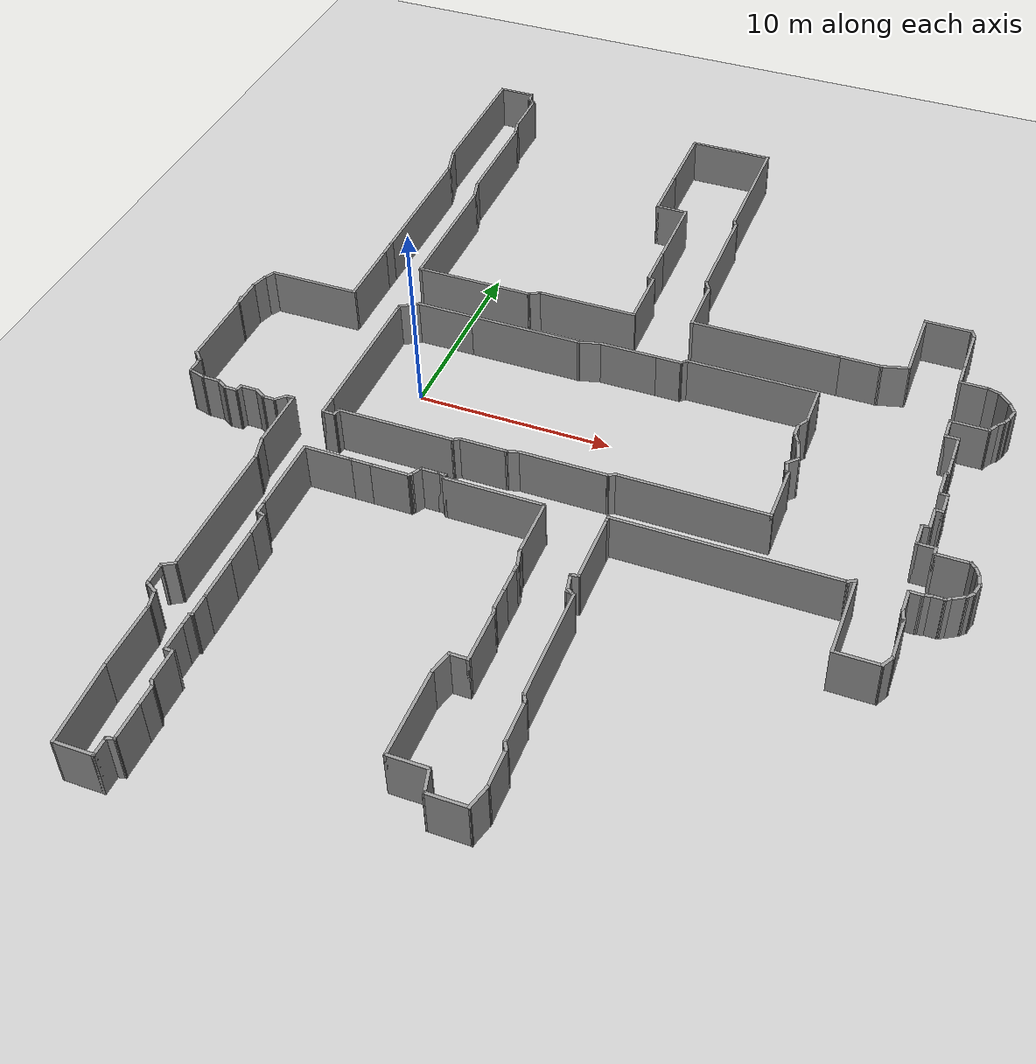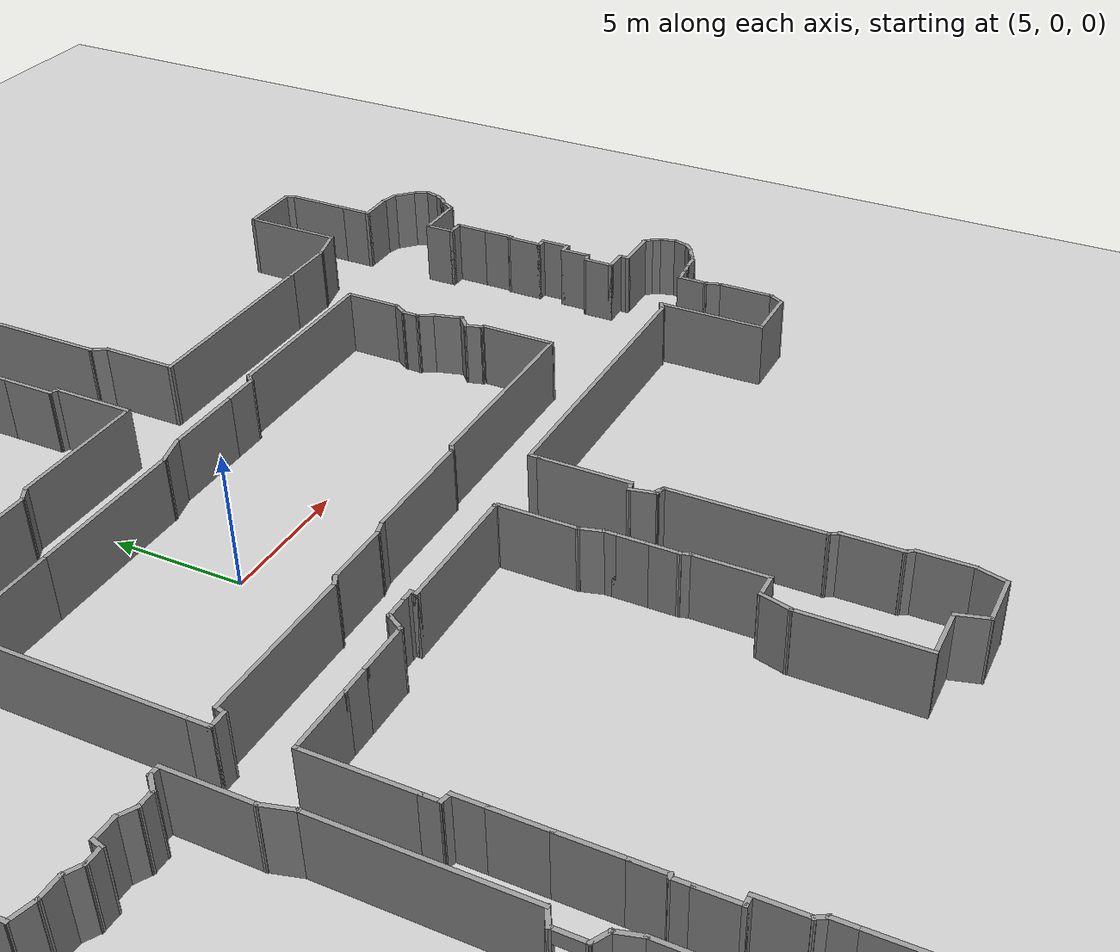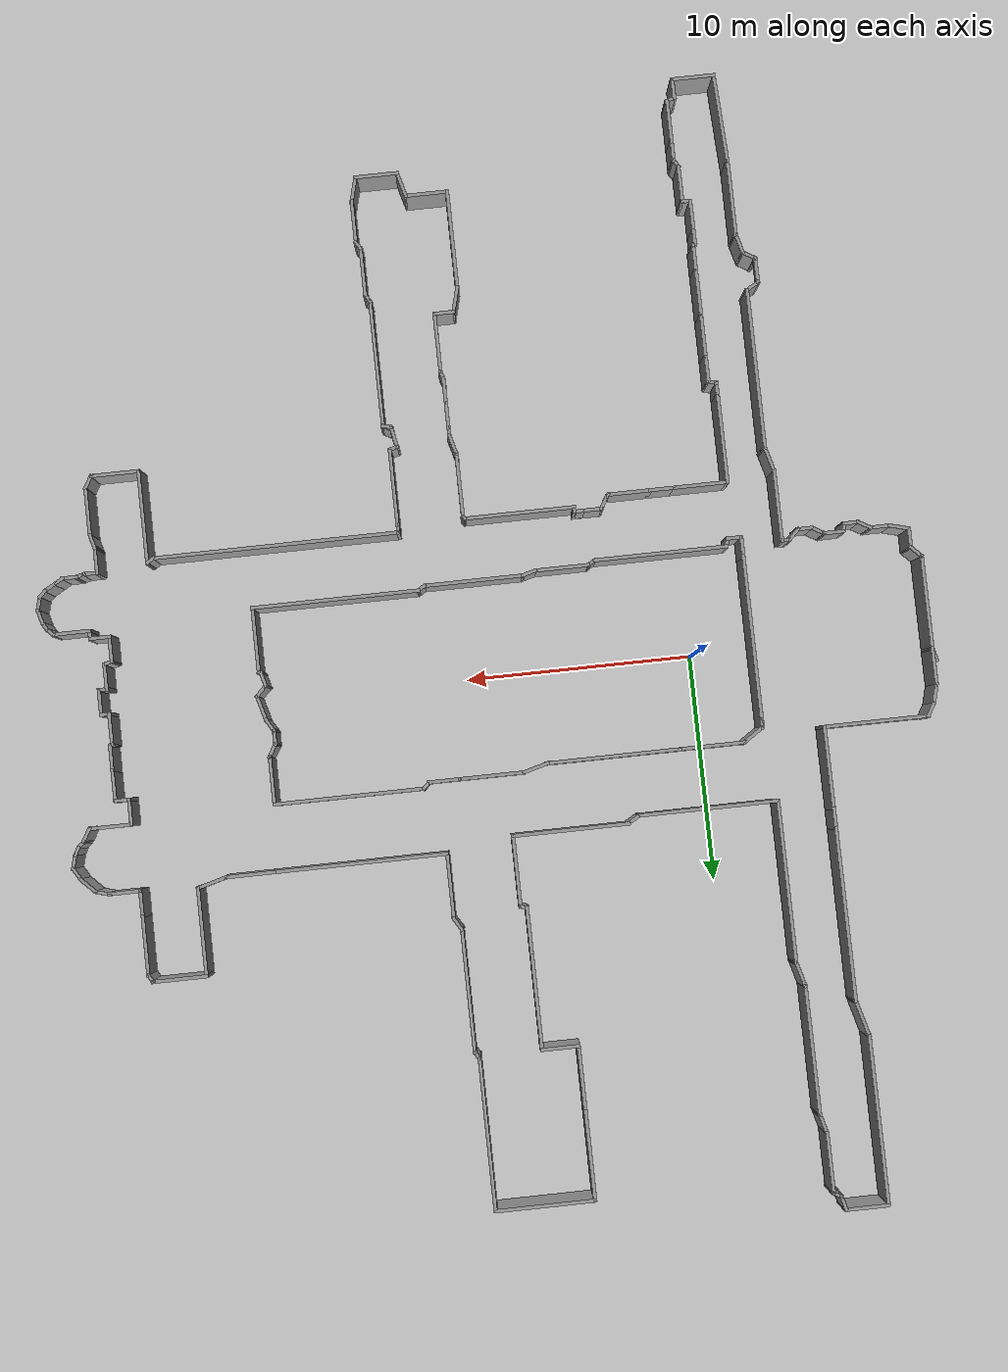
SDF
<sdf version="1.7">
 <world name="default">
  <light name="sun" type="directional">
   <pose>0 0 10 0 -0 0</pose>
   <diffuse>0.8 0.8 0.8 1</diffuse>
   <specular>0.2 0.2 0.2 1</specular>
   <attenuation>
    <range>1000</range>
    <constant>0.9</constant>
    <linear>0.01</linear>
    <quadratic>0.001</quadratic>
   </attenuation>
   <direction>-0.5 0.1 -0.9</direction>
   <spot><inner_angle>0</inner_angle><outer_angle>0</outer_angle><falloff>0</falloff></spot>
  </light>
  <model name="ground_plane">
   <static>1</static>
   <link name="link">
    <collision name="collision">
     <geometry><plane><normal>0 0 1</normal><size>100 100</size></plane></geometry>
     <surface><friction><ode><mu>100</mu><mu2>50</mu2></ode></friction></surface>
    </collision>
    <visual name="visual">
     <cast_shadows>0</cast_shadows>
     <geometry><plane><normal>0 0 1</normal><size>100 100</size></plane></geometry>
     <material>
      <script><uri>file://media/materials/scripts/gazebo.material</uri><name>Gazebo/Grey</name></script>
     </material>
    </visual>
   </link>
  </model>
  <gravity>0 0 -9.8</gravity>
  <magnetic_field>6e-06 2.3e-05 -4.2e-05</magnetic_field>
  <atmosphere type="adiabatic"/>
  <physics type="ode">
   <max_step_size>0.001</max_step_size>
   <real_time_factor>1</real_time_factor>
   <real_time_update_rate>1000</real_time_update_rate>
  </physics>
  <scene><ambient>0.4 0.4 0.4 1</ambient><background>0.7 0.7 0.7 1</background><shadows>1</shadows></scene>
  <audio><device>default</device></audio>
  <spherical_coordinates>
   <surface_model>EARTH_WGS84</surface_model>
   <latitude_deg>0</latitude_deg>
   <longitude_deg>0</longitude_deg>
   <elevation>0</elevation>
   <heading_deg>0</heading_deg>
  </spherical_coordinates>
  <model name="a10_simulation">
   <pose>8.94312 -0.455858 0 0 -0 0</pose>
   <link name="Wall_0">
    <collision name="Wall_0_Collision">
     <geometry><box><size>2 0.15 2.5</size></box></geometry>
     <pose>0 0 1.25 0 -0 0</pose>
    </collision>
    <visual name="Wall_0_Visual">
     <pose>0 0 1.25 0 -0 0</pose>
     <geometry><box><size>2 0.15 2.5</size></box></geometry>
     <material>
      <script><uri>file://media/materials/scripts/gazebo.material</uri><name>Gazebo/Grey</name></script>
      <ambient>1 1 1 1</ambient>
     </material>
     <meta><layer>0</layer></meta>
    </visual>
    <pose>-11.7781 -25.2008 0 0 -0 0</pose>
   </link>
   <link name="Wall_10">
    <collision name="Wall_10_Collision">
     <geometry><box><size>1.5 0.15 2.5</size></box></geometry>
     <pose>0 0 1.25 0 -0 0</pose>
    </collision>
    <visual name="Wall_10_Visual">
     <pose>0 0 1.25 0 -0 0</pose>
     <geometry><box><size>1.5 0.15 2.5</size></box></geometry>
     <material>
      <script><uri>file://media/materials/scripts/gazebo.material</uri><name>Gazebo/Grey</name></script>
      <ambient>1 1 1 1</ambient>
     </material>
     <meta><layer>0</layer></meta>
    </visual>
    <pose>-11.04 -18.9821 0 0 -0 1.5708</pose>
   </link>
   <link name="Wall_100">
    <collision name="Wall_100_Collision">
     <geometry><box><size>1.5 0.15 2.5</size></box></geometry>
     <pose>0 0 1.25 0 -0 0</pose>
    </collision>
    <visual name="Wall_100_Visual">
     <pose>0 0 1.25 0 -0 0</pose>
     <geometry><box><size>1.5 0.15 2.5</size></box></geometry>
     <material>
      <script><uri>file://media/materials/scripts/gazebo.material</uri><name>Gazebo/Grey</name></script>
      <ambient>1 1 1 1</ambient>
     </material>
     <meta><layer>0</layer></meta>
    </visual>
    <pose>16.9784 3.51275 0 0 -0 1.5708</pose>
   </link>
   <link name="Wall_101">
    <collision name="Wall_101_Collision">
     <geometry><box><size>0.75 0.15 2.5</size></box></geometry>
     <pose>0 0 1.25 0 -0 0</pose>
    </collision>
    <visual name="Wall_101_Visual">
     <pose>0 0 1.25 0 -0 0</pose>
     <geometry><box><size>0.75 0.15 2.5</size></box></geometry>
     <material>
      <script><uri>file://media/materials/scripts/gazebo.material</uri><name>Gazebo/Grey</name></script>
      <ambient>1 1 1 1</ambient>
     </material>
     <meta><layer>0</layer></meta>
    </visual>
    <pose>16.6784 4.18775 0 0 -0 3.14159</pose>
   </link>
   <link name="Wall_102">
    <collision name="Wall_102_Collision">
     <geometry><box><size>1.25 0.15 2.5</size></box></geometry>
     <pose>0 0 1.25 0 -0 0</pose>
    </collision>
    <visual name="Wall_102_Visual">
     <pose>0 0 1.25 0 -0 0</pose>
     <geometry><box><size>1.25 0.15 2.5</size></box></geometry>
     <material>
      <script><uri>file://media/materials/scripts/gazebo.material</uri><name>Gazebo/Grey</name></script>
      <ambient>1 1 1 1</ambient>
     </material>
     <meta><layer>0</layer></meta>
    </visual>
    <pose>16.3784 4.73775 0 0 -0 1.5708</pose>
   </link>
   <link name="Wall_103">
    <collision name="Wall_103_Collision">
     <geometry><box><size>2 0.15 2.5</size></box></geometry>
     <pose>0 0 1.25 0 -0 0</pose>
    </collision>
    <visual name="Wall_103_Visual">
     <pose>0 0 1.25 0 -0 0</pose>
     <geometry><box><size>2 0.15 2.5</size></box></geometry>
     <material>
      <script><uri>file://media/materials/scripts/gazebo.material</uri><name>Gazebo/Grey</name></script>
      <ambient>1 1 1 1</ambient>
     </material>
     <meta><layer>0</layer></meta>
    </visual>
    <pose>17.3034 5.28775 0 0 -0 0</pose>
   </link>
   <link name="Wall_104">
    <collision name="Wall_104_Collision">
     <geometry><box><size>0.75 0.15 2.5</size></box></geometry>
     <pose>0 0 1.25 0 -0 0</pose>
    </collision>
    <visual name="Wall_104_Visual">
     <pose>0 0 1.25 0 -0 0</pose>
     <geometry><box><size>0.75 0.15 2.5</size></box></geometry>
     <material>
      <script><uri>file://media/materials/scripts/gazebo.material</uri><name>Gazebo/Grey</name></script>
      <ambient>1 1 1 1</ambient>
     </material>
     <meta><layer>0</layer></meta>
    </visual>
    <pose>18.3784 5.54756 0 0 -0 1.0472</pose>
   </link>
   <link name="Wall_105">
    <collision name="Wall_105_Collision">
     <geometry><box><size>0.5 0.15 2.5</size></box></geometry>
     <pose>0 0 1.25 0 -0 0</pose>
    </collision>
    <visual name="Wall_105_Visual">
     <pose>0 0 1.25 0 -0 0</pose>
     <geometry><box><size>0.5 0.15 2.5</size></box></geometry>
     <material>
      <script><uri>file://media/materials/scripts/gazebo.material</uri><name>Gazebo/Grey</name></script>
      <ambient>1 1 1 1</ambient>
     </material>
     <meta><layer>0</layer></meta>
    </visual>
    <pose>18.6522 5.93111 0 0 -0 0.785398</pose>
   </link>
   <link name="Wall_106">
    <collision name="Wall_106_Collision">
     <geometry><box><size>0.5 0.15 2.5</size></box></geometry>
     <pose>0 0 1.25 0 -0 0</pose>
    </collision>
    <visual name="Wall_106_Visual">
     <pose>0 0 1.25 0 -0 0</pose>
     <geometry><box><size>0.5 0.15 2.5</size></box></geometry>
     <material>
      <script><uri>file://media/materials/scripts/gazebo.material</uri><name>Gazebo/Grey</name></script>
      <ambient>1 1 1 1</ambient>
     </material>
     <meta><layer>0</layer></meta>
    </visual>
    <pose>18.8634 6.20641 0 0 -0 1.0472</pose>
   </link>
   <link name="Wall_107">
    <collision name="Wall_107_Collision">
     <geometry><box><size>0.75 0.15 2.5</size></box></geometry>
     <pose>0 0 1.25 0 -0 0</pose>
    </collision>
    <visual name="Wall_107_Visual">
     <pose>0 0 1.25 0 -0 0</pose>
     <geometry><box><size>0.75 0.15 2.5</size></box></geometry>
     <material>
      <script><uri>file://media/materials/scripts/gazebo.material</uri><name>Gazebo/Grey</name></script>
      <ambient>1 1 1 1</ambient>
     </material>
     <meta><layer>0</layer></meta>
    </visual>
    <pose>19.0286 6.64774 0 0 -0 1.309</pose>
   </link>
   <link name="Wall_108">
    <collision name="Wall_108_Collision">
     <geometry><box><size>0.75 0.15 2.5</size></box></geometry>
     <pose>0 0 1.25 0 -0 0</pose>
    </collision>
    <visual name="Wall_108_Visual">
     <pose>0 0 1.25 0 -0 0</pose>
     <geometry><box><size>0.75 0.15 2.5</size></box></geometry>
     <material>
      <script><uri>file://media/materials/scripts/gazebo.material</uri><name>Gazebo/Grey</name></script>
      <ambient>1 1 1 1</ambient>
     </material>
     <meta><layer>0</layer></meta>
    </visual>
    <pose>18.9562 7.19732 0 0 -0 2.0944</pose>
   </link>
   <link name="Wall_109">
    <collision name="Wall_109_Collision">
     <geometry><box><size>1 0.15 2.5</size></box></geometry>
     <pose>0 0 1.25 0 -0 0</pose>
    </collision>
    <visual name="Wall_109_Visual">
     <pose>0 0 1.25 0 -0 0</pose>
     <geometry><box><size>1 0.15 2.5</size></box></geometry>
     <material>
      <script><uri>file://media/materials/scripts/gazebo.material</uri><name>Gazebo/Grey</name></script>
      <ambient>1 1 1 1</ambient>
     </material>
     <meta><layer>0</layer></meta>
    </visual>
    <pose>18.5057 7.75765 0 0 -0 2.35619</pose>
   </link>
   <link name="Wall_11">
    <collision name="Wall_11_Collision">
     <geometry><box><size>0.75 0.15 2.5</size></box></geometry>
     <pose>0 0 1.25 0 -0 0</pose>
    </collision>
    <visual name="Wall_11_Visual">
     <pose>0 0 1.25 0 -0 0</pose>
     <geometry><box><size>0.75 0.15 2.5</size></box></geometry>
     <material>
      <script><uri>file://media/materials/scripts/gazebo.material</uri><name>Gazebo/Grey</name></script>
      <ambient>1 1 1 1</ambient>
     </material>
     <meta><layer>0</layer></meta>
    </visual>
    <pose>-11.04 -18.0071 0 0 -0 1.5708</pose>
   </link>
   <link name="Wall_111">
    <collision name="Wall_111_Collision">
     <geometry><box><size>0.75 0.15 2.5</size></box></geometry>
     <pose>0 0 1.25 0 -0 0</pose>
    </collision>
    <visual name="Wall_111_Visual">
     <pose>0 0 1.25 0 -0 0</pose>
     <geometry><box><size>0.75 0.15 2.5</size></box></geometry>
     <material>
      <script><uri>file://media/materials/scripts/gazebo.material</uri><name>Gazebo/Grey</name></script>
      <ambient>1 1 1 1</ambient>
     </material>
     <meta><layer>0</layer></meta>
    </visual>
    <pose>17.9154 8.13582 0 0 -0 2.87979</pose>
   </link>
   <link name="Wall_112">
    <collision name="Wall_112_Collision">
     <geometry><box><size>1.5 0.15 2.5</size></box></geometry>
     <pose>0 0 1.25 0 -0 0</pose>
    </collision>
    <visual name="Wall_112_Visual">
     <pose>0 0 1.25 0 -0 0</pose>
     <geometry><box><size>1.5 0.15 2.5</size></box></geometry>
     <material>
      <script><uri>file://media/materials/scripts/gazebo.material</uri><name>Gazebo/Grey</name></script>
      <ambient>1 1 1 1</ambient>
     </material>
     <meta><layer>0</layer></meta>
    </visual>
    <pose>16.9506 8.21346 0 0 -0 3.14159</pose>
   </link>
   <link name="Wall_113">
    <collision name="Wall_113_Collision">
     <geometry><box><size>1.25 0.15 2.5</size></box></geometry>
     <pose>0 0 1.25 0 -0 0</pose>
    </collision>
    <visual name="Wall_113_Visual">
     <pose>0 0 1.25 0 -0 0</pose>
     <geometry><box><size>1.25 0.15 2.5</size></box></geometry>
     <material>
      <script><uri>file://media/materials/scripts/gazebo.material</uri><name>Gazebo/Grey</name></script>
      <ambient>1 1 1 1</ambient>
     </material>
     <meta><layer>0</layer></meta>
    </visual>
    <pose>16.2756 8.76346 0 0 -0 1.5708</pose>
   </link>
   <link name="Wall_114">
    <collision name="Wall_114_Collision">
     <geometry><box><size>2.75 0.15 2.5</size></box></geometry>
     <pose>0 0 1.25 0 -0 0</pose>
    </collision>
    <visual name="Wall_114_Visual">
     <pose>0 0 1.25 0 -0 0</pose>
     <geometry><box><size>2.75 0.15 2.5</size></box></geometry>
     <material>
      <script><uri>file://media/materials/scripts/gazebo.material</uri><name>Gazebo/Grey</name></script>
      <ambient>1 1 1 1</ambient>
     </material>
     <meta><layer>0</layer></meta>
    </visual>
    <pose>16.2756 10.6135 0 0 -0 1.5708</pose>
   </link>
   <link name="Wall_115">
    <collision name="Wall_115_Collision">
     <geometry><box><size>0.5 0.15 2.5</size></box></geometry>
     <pose>0 0 1.25 0 -0 0</pose>
    </collision>
    <visual name="Wall_115_Visual">
     <pose>0 0 1.25 0 -0 0</pose>
     <geometry><box><size>0.5 0.15 2.5</size></box></geometry>
     <material>
      <script><uri>file://media/materials/scripts/gazebo.material</uri><name>Gazebo/Grey</name></script>
      <ambient>1 1 1 1</ambient>
     </material>
     <meta><layer>0</layer></meta>
    </visual>
    <pose>16.1881 12.065 0 0 -0 2.0944</pose>
   </link>
   <link name="Wall_116">
    <collision name="Wall_116_Collision">
     <geometry><box><size>2.5 0.15 2.5</size></box></geometry>
     <pose>0 0 1.25 0 -0 0</pose>
    </collision>
    <visual name="Wall_116_Visual">
     <pose>0 0 1.25 0 -0 0</pose>
     <geometry><box><size>2.5 0.15 2.5</size></box></geometry>
     <material>
      <script><uri>file://media/materials/scripts/gazebo.material</uri><name>Gazebo/Grey</name></script>
      <ambient>1 1 1 1</ambient>
     </material>
     <meta><layer>0</layer></meta>
    </visual>
    <pose>14.9256 12.2166 0 0 -0 3.14159</pose>
   </link>
   <link name="Wall_117">
    <collision name="Wall_117_Collision">
     <geometry><box><size>4 0.15 2.5</size></box></geometry>
     <pose>0 0 1.25 0 -0 0</pose>
    </collision>
    <visual name="Wall_117_Visual">
     <pose>0 0 1.25 0 -0 0</pose>
     <geometry><box><size>4 0.15 2.5</size></box></geometry>
     <material>
      <script><uri>file://media/materials/scripts/gazebo.material</uri><name>Gazebo/Grey</name></script>
      <ambient>1 1 1 1</ambient>
     </material>
     <meta><layer>0</layer></meta>
    </visual>
    <pose>13.7506 10.2916 0 0 -0 -1.5708</pose>
   </link>
   <link name="Wall_118">
    <collision name="Wall_118_Collision">
     <geometry><box><size>1.5 0.15 2.5</size></box></geometry>
     <pose>0 0 1.25 0 -0 0</pose>
    </collision>
    <visual name="Wall_118_Visual">
     <pose>0 0 1.25 0 -0 0</pose>
     <geometry><box><size>1.5 0.15 2.5</size></box></geometry>
     <material>
      <script><uri>file://media/materials/scripts/gazebo.material</uri><name>Gazebo/Grey</name></script>
      <ambient>1 1 1 1</ambient>
     </material>
     <meta><layer>0</layer></meta>
    </visual>
    <pose>13.0986 8.19187 0 0 -0 -2.87979</pose>
   </link>
   <link name="Wall_119">
    <collision name="Wall_119_Collision">
     <geometry><box><size>2.25 0.15 2.5</size></box></geometry>
     <pose>0 0 1.25 0 -0 0</pose>
    </collision>
    <visual name="Wall_119_Visual">
     <pose>0 0 1.25 0 -0 0</pose>
     <geometry><box><size>2.25 0.15 2.5</size></box></geometry>
     <material>
      <script><uri>file://media/materials/scripts/gazebo.material</uri><name>Gazebo/Grey</name></script>
      <ambient>1 1 1 1</ambient>
     </material>
     <meta><layer>0</layer></meta>
    </visual>
    <pose>11.3966 8.01717 0 0 -0 3.14159</pose>
   </link>
   <link name="Wall_12">
    <collision name="Wall_12_Collision">
     <geometry><box><size>0.25 0.15 2.5</size></box></geometry>
     <pose>0 0 1.25 0 -0 0</pose>
    </collision>
    <visual name="Wall_12_Visual">
     <pose>0 0 1.25 0 -0 0</pose>
     <geometry><box><size>0.25 0.15 2.5</size></box></geometry>
     <material>
      <script><uri>file://media/materials/scripts/gazebo.material</uri><name>Gazebo/Grey</name></script>
      <ambient>1 1 1 1</ambient>
     </material>
     <meta><layer>0</layer></meta>
    </visual>
    <pose>-10.9967 -17.6821 0 0 -0 0.523599</pose>
   </link>
   <link name="Wall_120">
    <collision name="Wall_120_Collision">
     <geometry><box><size>7.75 0.15 2.5</size></box></geometry>
     <pose>0 0 1.25 0 -0 0</pose>
    </collision>
    <visual name="Wall_120_Visual">
     <pose>0 0 1.25 0 -0 0</pose>
     <geometry><box><size>7.75 0.15 2.5</size></box></geometry>
     <material>
      <script><uri>file://media/materials/scripts/gazebo.material</uri><name>Gazebo/Grey</name></script>
      <ambient>1 1 1 1</ambient>
     </material>
     <meta><layer>0</layer></meta>
    </visual>
    <pose>6.54662 8.01717 0 0 -0 3.14159</pose>
   </link>
   <link name="Wall_121">
    <collision name="Wall_121_Collision">
     <geometry><box><size>3 0.15 2.5</size></box></geometry>
     <pose>0 0 1.25 0 -0 0</pose>
    </collision>
    <visual name="Wall_121_Visual">
     <pose>0 0 1.25 0 -0 0</pose>
     <geometry><box><size>3 0.15 2.5</size></box></geometry>
     <material>
      <script><uri>file://media/materials/scripts/gazebo.material</uri><name>Gazebo/Grey</name></script>
      <ambient>1 1 1 1</ambient>
     </material>
     <meta><layer>0</layer></meta>
    </visual>
    <pose>2.74662 9.44217 0 0 -0 1.5708</pose>
   </link>
   <link name="Wall_122">
    <collision name="Wall_122_Collision">
     <geometry><box><size>0.75 0.15 2.5</size></box></geometry>
     <pose>0 0 1.25 0 -0 0</pose>
    </collision>
    <visual name="Wall_122_Visual">
     <pose>0 0 1.25 0 -0 0</pose>
     <geometry><box><size>0.75 0.15 2.5</size></box></geometry>
     <material>
      <script><uri>file://media/materials/scripts/gazebo.material</uri><name>Gazebo/Grey</name></script>
      <ambient>1 1 1 1</ambient>
     </material>
     <meta><layer>0</layer></meta>
    </visual>
    <pose>2.59662 11.127 0 0 -0 2.0944</pose>
   </link>
   <link name="Wall_123">
    <collision name="Wall_123_Collision">
     <geometry><box><size>5.5 0.15 2.5</size></box></geometry>
     <pose>0 0 1.25 0 -0 0</pose>
    </collision>
    <visual name="Wall_123_Visual">
     <pose>0 0 1.25 0 -0 0</pose>
     <geometry><box><size>5.5 0.15 2.5</size></box></geometry>
     <material>
      <script><uri>file://media/materials/scripts/gazebo.material</uri><name>Gazebo/Grey</name></script>
      <ambient>1 1 1 1</ambient>
     </material>
     <meta><layer>0</layer></meta>
    </visual>
    <pose>2.44662 14.0618 0 0 -0 1.5708</pose>
   </link>
   <link name="Wall_125">
    <collision name="Wall_125_Collision">
     <geometry><box><size>0.5 0.15 2.5</size></box></geometry>
     <pose>0 0 1.25 0 -0 0</pose>
    </collision>
    <visual name="Wall_125_Visual">
     <pose>0 0 1.25 0 -0 0</pose>
     <geometry><box><size>0.5 0.15 2.5</size></box></geometry>
     <material>
      <script><uri>file://media/materials/scripts/gazebo.material</uri><name>Gazebo/Grey</name></script>
      <ambient>1 1 1 1</ambient>
     </material>
     <meta><layer>0</layer></meta>
    </visual>
    <pose>2.35912 16.8883 0 0 -0 2.0944</pose>
   </link>
   <link name="Wall_126">
    <collision name="Wall_126_Collision">
     <geometry><box><size>6.75 0.15 2.5</size></box></geometry>
     <pose>0 0 1.25 0 -0 0</pose>
    </collision>
    <visual name="Wall_126_Visual">
     <pose>0 0 1.25 0 -0 0</pose>
     <geometry><box><size>6.75 0.15 2.5</size></box></geometry>
     <material>
      <script><uri>file://media/materials/scripts/gazebo.material</uri><name>Gazebo/Grey</name></script>
      <ambient>1 1 1 1</ambient>
     </material>
     <meta><layer>0</layer></meta>
    </visual>
    <pose>2.27162 20.3399 0 0 -0 1.5708</pose>
   </link>
   <link name="Wall_127">
    <collision name="Wall_127_Collision">
     <geometry><box><size>4.5 0.15 2.5</size></box></geometry>
     <pose>0 0 1.25 0 -0 0</pose>
    </collision>
    <visual name="Wall_127_Visual">
     <pose>0 0 1.25 0 -0 0</pose>
     <geometry><box><size>4.5 0.15 2.5</size></box></geometry>
     <material>
      <script><uri>file://media/materials/scripts/gazebo.material</uri><name>Gazebo/Grey</name></script>
      <ambient>1 1 1 1</ambient>
     </material>
     <meta><layer>0</layer></meta>
    </visual>
    <pose>0.096621 23.6399 0 0 -0 3.14159</pose>
   </link>
   <link name="Wall_128">
    <collision name="Wall_128_Collision">
     <geometry><box><size>4 0.15 2.5</size></box></geometry>
     <pose>0 0 1.25 0 -0 0</pose>
    </collision>
    <visual name="Wall_128_Visual">
     <pose>0 0 1.25 0 -0 0</pose>
     <geometry><box><size>4 0.15 2.5</size></box></geometry>
     <material>
      <script><uri>file://media/materials/scripts/gazebo.material</uri><name>Gazebo/Grey</name></script>
      <ambient>1 1 1 1</ambient>
     </material>
     <meta><layer>0</layer></meta>
    </visual>
    <pose>-2.07838 21.7149 0 0 -0 -1.5708</pose>
   </link>
   <link name="Wall_129">
    <collision name="Wall_129_Collision">
     <geometry><box><size>3 0.15 2.5</size></box></geometry>
     <pose>0 0 1.25 0 -0 0</pose>
    </collision>
    <visual name="Wall_129_Visual">
     <pose>0 0 1.25 0 -0 0</pose>
     <geometry><box><size>3 0.15 2.5</size></box></geometry>
     <material>
      <script><uri>file://media/materials/scripts/gazebo.material</uri><name>Gazebo/Grey</name></script>
      <ambient>1 1 1 1</ambient>
     </material>
     <meta><layer>0</layer></meta>
    </visual>
    <pose>-2.07838 18.3649 0 0 -0 -1.5708</pose>
   </link>
   <link name="Wall_13">
    <collision name="Wall_13_Collision">
     <geometry><box><size>1.25 0.15 2.5</size></box></geometry>
     <pose>0 0 1.25 0 -0 0</pose>
    </collision>
    <visual name="Wall_13_Visual">
     <pose>0 0 1.25 0 -0 0</pose>
     <geometry><box><size>1.25 0.15 2.5</size></box></geometry>
     <material>
      <script><uri>file://media/materials/scripts/gazebo.material</uri><name>Gazebo/Grey</name></script>
      <ambient>1 1 1 1</ambient>
     </material>
     <meta><layer>0</layer></meta>
    </visual>
    <pose>-10.9534 -17.1071 0 0 -0 1.5708</pose>
   </link>
   <link name="Wall_130">
    <collision name="Wall_130_Collision">
     <geometry><box><size>1.75 0.15 2.5</size></box></geometry>
     <pose>0 0 1.25 0 -0 0</pose>
    </collision>
    <visual name="Wall_130_Visual">
     <pose>0 0 1.25 0 -0 0</pose>
     <geometry><box><size>1.75 0.15 2.5</size></box></geometry>
     <material>
      <script><uri>file://media/materials/scripts/gazebo.material</uri><name>Gazebo/Grey</name></script>
      <ambient>1 1 1 1</ambient>
     </material>
     <meta><layer>0</layer></meta>
    </visual>
    <pose>-1.27838 16.9399 0 0 -0 0</pose>
   </link>
   <link name="Wall_131">
    <collision name="Wall_131_Collision">
     <geometry><box><size>4.25 0.15 2.5</size></box></geometry>
     <pose>0 0 1.25 0 -0 0</pose>
    </collision>
    <visual name="Wall_131_Visual">
     <pose>0 0 1.25 0 -0 0</pose>
     <geometry><box><size>4.25 0.15 2.5</size></box></geometry>
     <material>
      <script><uri>file://media/materials/scripts/gazebo.material</uri><name>Gazebo/Grey</name></script>
      <ambient>1 1 1 1</ambient>
     </material>
     <meta><layer>0</layer></meta>
    </visual>
    <pose>-0.478379 14.8899 0 0 -0 -1.5708</pose>
   </link>
   <link name="Wall_133">
    <collision name="Wall_133_Collision">
     <geometry><box><size>2.25 0.15 2.5</size></box></geometry>
     <pose>0 0 1.25 0 -0 0</pose>
    </collision>
    <visual name="Wall_133_Visual">
     <pose>0 0 1.25 0 -0 0</pose>
     <geometry><box><size>2.25 0.15 2.5</size></box></geometry>
     <material>
      <script><uri>file://media/materials/scripts/gazebo.material</uri><name>Gazebo/Grey</name></script>
      <ambient>1 1 1 1</ambient>
     </material>
     <meta><layer>0</layer></meta>
    </visual>
    <pose>-0.478379 11.7899 0 0 -0 -1.5708</pose>
   </link>
   <link name="Wall_134">
    <collision name="Wall_134_Collision">
     <geometry><box><size>0.424124 0.15 2.5</size></box></geometry>
     <pose>0 0 1.25 0 -0 0</pose>
    </collision>
    <visual name="Wall_134_Visual">
     <pose>0 0 1.25 0 -0 0</pose>
     <geometry><box><size>0.424124 0.15 2.5</size></box></geometry>
     <material>
      <script><uri>file://media/materials/scripts/gazebo.material</uri><name>Gazebo/Grey</name></script>
      <ambient>1 1 1 1</ambient>
     </material>
     <meta><layer>0</layer></meta>
    </visual>
    <pose>-0.349018 10.6946 0 0 -0 -0.336789</pose>
   </link>
   <link name="Wall_135">
    <collision name="Wall_135_Collision">
     <geometry><box><size>3.25 0.15 2.5</size></box></geometry>
     <pose>0 0 1.25 0 -0 0</pose>
    </collision>
    <visual name="Wall_135_Visual">
     <pose>0 0 1.25 0 -0 0</pose>
     <geometry><box><size>3.25 0.15 2.5</size></box></geometry>
     <material>
      <script><uri>file://media/materials/scripts/gazebo.material</uri><name>Gazebo/Grey</name></script>
      <ambient>1 1 1 1</ambient>
     </material>
     <meta><layer>0</layer></meta>
    </visual>
    <pose>-0.20643 9.0993 0 0 -0 -1.5708</pose>
   </link>
   <link name="Wall_138">
    <collision name="Wall_138_Collision">
     <geometry><box><size>5.25 0.15 2.5</size></box></geometry>
     <pose>0 0 1.25 0 -0 0</pose>
    </collision>
    <visual name="Wall_138_Visual">
     <pose>0 0 1.25 0 -0 0</pose>
     <geometry><box><size>5.25 0.15 2.5</size></box></geometry>
     <material>
      <script><uri>file://media/materials/scripts/gazebo.material</uri><name>Gazebo/Grey</name></script>
      <ambient>1 1 1 1</ambient>
     </material>
     <meta><layer>0</layer></meta>
    </visual>
    <pose>-2.75643 7.5493 0 0 -0 3.14159</pose>
   </link>
   <link name="Wall_139">
    <collision name="Wall_139_Collision">
     <geometry><box><size>0.75 0.15 2.5</size></box></geometry>
     <pose>0 0 1.25 0 -0 0</pose>
    </collision>
    <visual name="Wall_139_Visual">
     <pose>0 0 1.25 0 -0 0</pose>
     <geometry><box><size>0.75 0.15 2.5</size></box></geometry>
     <material>
      <script><uri>file://media/materials/scripts/gazebo.material</uri><name>Gazebo/Grey</name></script>
      <ambient>1 1 1 1</ambient>
     </material>
     <meta><layer>0</layer></meta>
    </visual>
    <pose>-5.56624 7.3993 0 0 -0 -2.61799</pose>
   </link>
   <link name="Wall_14">
    <collision name="Wall_14_Collision">
     <geometry><box><size>2.25 0.15 2.5</size></box></geometry>
     <pose>0 0 1.25 0 -0 0</pose>
    </collision>
    <visual name="Wall_14_Visual">
     <pose>0 0 1.25 0 -0 0</pose>
     <geometry><box><size>2.25 0.15 2.5</size></box></geometry>
     <material>
      <script><uri>file://media/materials/scripts/gazebo.material</uri><name>Gazebo/Grey</name></script>
      <ambient>1 1 1 1</ambient>
     </material>
     <meta><layer>0</layer></meta>
    </visual>
    <pose>-10.9534 -15.5071 0 0 -0 1.5708</pose>
   </link>
   <link name="Wall_140">
    <collision name="Wall_140_Collision">
     <geometry><box><size>6.25 0.15 2.5</size></box></geometry>
     <pose>0 0 1.25 0 -0 0</pose>
    </collision>
    <visual name="Wall_140_Visual">
     <pose>0 0 1.25 0 -0 0</pose>
     <geometry><box><size>6.25 0.15 2.5</size></box></geometry>
     <material>
      <script><uri>file://media/materials/scripts/gazebo.material</uri><name>Gazebo/Grey</name></script>
      <ambient>1 1 1 1</ambient>
     </material>
     <meta><layer>0</layer></meta>
    </visual>
    <pose>-8.87604 7.2493 0 0 -0 3.14159</pose>
   </link>
   <link name="Wall_142">
    <collision name="Wall_142_Collision">
     <geometry><box><size>7.25 0.15 2.5</size></box></geometry>
     <pose>0 0 1.25 0 -0 0</pose>
    </collision>
    <visual name="Wall_142_Visual">
     <pose>0 0 1.25 0 -0 0</pose>
     <geometry><box><size>7.25 0.15 2.5</size></box></geometry>
     <material>
      <script><uri>file://media/materials/scripts/gazebo.material</uri><name>Gazebo/Grey</name></script>
      <ambient>1 1 1 1</ambient>
     </material>
     <meta><layer>0</layer></meta>
    </visual>
    <pose>-11.926 10.7993 0 0 -0 1.5708</pose>
   </link>
   <link name="Wall_143">
    <collision name="Wall_143_Collision">
     <geometry><box><size>1.25 0.15 2.5</size></box></geometry>
     <pose>0 0 1.25 0 -0 0</pose>
    </collision>
    <visual name="Wall_143_Visual">
     <pose>0 0 1.25 0 -0 0</pose>
     <geometry><box><size>1.25 0.15 2.5</size></box></geometry>
     <material>
      <script><uri>file://media/materials/scripts/gazebo.material</uri><name>Gazebo/Grey</name></script>
      <ambient>1 1 1 1</ambient>
     </material>
     <meta><layer>0</layer></meta>
    </visual>
    <pose>-12.0684 14.8806 0 0 -0 1.8326</pose>
   </link>
   <link name="Wall_144">
    <collision name="Wall_144_Collision">
     <geometry><box><size>5.75 0.15 2.5</size></box></geometry>
     <pose>0 0 1.25 0 -0 0</pose>
    </collision>
    <visual name="Wall_144_Visual">
     <pose>0 0 1.25 0 -0 0</pose>
     <geometry><box><size>5.75 0.15 2.5</size></box></geometry>
     <material>
      <script><uri>file://media/materials/scripts/gazebo.material</uri><name>Gazebo/Grey</name></script>
      <ambient>1 1 1 1</ambient>
     </material>
     <meta><layer>0</layer></meta>
    </visual>
    <pose>-12.2107 18.2118 0 0 -0 1.5708</pose>
   </link>
   <link name="Wall_145">
    <collision name="Wall_145_Collision">
     <geometry><box><size>1 0.15 2.5</size></box></geometry>
     <pose>0 0 1.25 0 -0 0</pose>
    </collision>
    <visual name="Wall_145_Visual">
     <pose>0 0 1.25 0 -0 0</pose>
     <geometry><box><size>1 0.15 2.5</size></box></geometry>
     <material>
      <script><uri>file://media/materials/scripts/gazebo.material</uri><name>Gazebo/Grey</name></script>
      <ambient>1 1 1 1</ambient>
     </material>
     <meta><layer>0</layer></meta>
    </visual>
    <pose>-12.3207 21.4223 0 0 -0 1.8326</pose>
   </link>
   <link name="Wall_146">
    <collision name="Wall_146_Collision">
     <geometry><box><size>2.75 0.15 2.5</size></box></geometry>
     <pose>0 0 1.25 0 -0 0</pose>
    </collision>
    <visual name="Wall_146_Visual">
     <pose>0 0 1.25 0 -0 0</pose>
     <geometry><box><size>2.75 0.15 2.5</size></box></geometry>
     <material>
      <script><uri>file://media/materials/scripts/gazebo.material</uri><name>Gazebo/Grey</name></script>
      <ambient>1 1 1 1</ambient>
     </material>
     <meta><layer>0</layer></meta>
    </visual>
    <pose>-12.4307 23.1329 0 0 -0 1.5708</pose>
   </link>
   <link name="Wall_147">
    <collision name="Wall_147_Collision">
     <geometry><box><size>0.5 0.15 2.5</size></box></geometry>
     <pose>0 0 1.25 0 -0 0</pose>
    </collision>
    <visual name="Wall_147_Visual">
     <pose>0 0 1.25 0 -0 0</pose>
     <geometry><box><size>0.5 0.15 2.5</size></box></geometry>
     <material>
      <script><uri>file://media/materials/scripts/gazebo.material</uri><name>Gazebo/Grey</name></script>
      <ambient>1 1 1 1</ambient>
     </material>
     <meta><layer>0</layer></meta>
    </visual>
    <pose>-12.5823 24.5204 0 0 -0 2.61799</pose>
   </link>
   <link name="Wall_149">
    <collision name="Wall_149_Collision">
     <geometry><box><size>0.5 0.15 2.5</size></box></geometry>
     <pose>0 0 1.25 0 -0 0</pose>
    </collision>
    <visual name="Wall_149_Visual">
     <pose>0 0 1.25 0 -0 0</pose>
     <geometry><box><size>0.5 0.15 2.5</size></box></geometry>
     <material>
      <script><uri>file://media/materials/scripts/gazebo.material</uri><name>Gazebo/Grey</name></script>
      <ambient>1 1 1 1</ambient>
     </material>
     <meta><layer>0</layer></meta>
    </visual>
    <pose>-12.5823 24.5204 0 0 -0 2.61799</pose>
   </link>
   <link name="Wall_150">
    <collision name="Wall_150_Collision">
     <geometry><box><size>0.75 0.15 2.5</size></box></geometry>
     <pose>0 0 1.25 0 -0 0</pose>
    </collision>
    <visual name="Wall_150_Visual">
     <pose>0 0 1.25 0 -0 0</pose>
     <geometry><box><size>0.75 0.15 2.5</size></box></geometry>
     <material>
      <script><uri>file://media/materials/scripts/gazebo.material</uri><name>Gazebo/Grey</name></script>
      <ambient>1 1 1 1</ambient>
     </material>
     <meta><layer>0</layer></meta>
    </visual>
    <pose>-12.8115 24.8976 0 0 -0 1.8326</pose>
   </link>
   <link name="Wall_151">
    <collision name="Wall_151_Collision">
     <geometry><box><size>2 0.15 2.5</size></box></geometry>
     <pose>0 0 1.25 0 -0 0</pose>
    </collision>
    <visual name="Wall_151_Visual">
     <pose>0 0 1.25 0 -0 0</pose>
     <geometry><box><size>2 0.15 2.5</size></box></geometry>
     <material>
      <script><uri>file://media/materials/scripts/gazebo.material</uri><name>Gazebo/Grey</name></script>
      <ambient>1 1 1 1</ambient>
     </material>
     <meta><layer>0</layer></meta>
    </visual>
    <pose>-13.8141 25.1874 0 0 -0 3.14159</pose>
   </link>
   <link name="Wall_152">
    <collision name="Wall_152_Collision">
     <geometry><box><size>7.5 0.15 2.5</size></box></geometry>
     <pose>0 0 1.25 0 -0 0</pose>
    </collision>
    <visual name="Wall_152_Visual">
     <pose>0 0 1.25 0 -0 0</pose>
     <geometry><box><size>7.5 0.15 2.5</size></box></geometry>
     <material>
      <script><uri>file://media/materials/scripts/gazebo.material</uri><name>Gazebo/Grey</name></script>
      <ambient>1 1 1 1</ambient>
     </material>
     <meta><layer>0</layer></meta>
    </visual>
    <pose>-14.7391 21.5124 0 0 -0 -1.5708</pose>
   </link>
   <link name="Wall_153">
    <collision name="Wall_153_Collision">
     <geometry><box><size>1.75 0.15 2.5</size></box></geometry>
     <pose>0 0 1.25 0 -0 0</pose>
    </collision>
    <visual name="Wall_153_Visual">
     <pose>0 0 1.25 0 -0 0</pose>
     <geometry><box><size>1.75 0.15 2.5</size></box></geometry>
     <material>
      <script><uri>file://media/materials/scripts/gazebo.material</uri><name>Gazebo/Grey</name></script>
      <ambient>1 1 1 1</ambient>
     </material>
     <meta><layer>0</layer></meta>
    </visual>
    <pose>-14.5321 17.0647 0 0 -0 -1.309</pose>
   </link>
   <link name="Wall_154">
    <collision name="Wall_154_Collision">
     <geometry><box><size>7.75 0.15 2.5</size></box></geometry>
     <pose>0 0 1.25 0 -0 0</pose>
    </collision>
    <visual name="Wall_154_Visual">
     <pose>0 0 1.25 0 -0 0</pose>
     <geometry><box><size>7.75 0.15 2.5</size></box></geometry>
     <material>
      <script><uri>file://media/materials/scripts/gazebo.material</uri><name>Gazebo/Grey</name></script>
      <ambient>1 1 1 1</ambient>
     </material>
     <meta><layer>0</layer></meta>
    </visual>
    <pose>-14.325 12.4919 0 0 -0 -1.5708</pose>
   </link>
   <link name="Wall_156">
    <collision name="Wall_156_Collision">
     <geometry><box><size>1 0.15 2.5</size></box></geometry>
     <pose>0 0 1.25 0 -0 0</pose>
    </collision>
    <visual name="Wall_156_Visual">
     <pose>0 0 1.25 0 -0 0</pose>
     <geometry><box><size>1 0.15 2.5</size></box></geometry>
     <material>
      <script><uri>file://media/materials/scripts/gazebo.material</uri><name>Gazebo/Grey</name></script>
      <ambient>1 1 1 1</ambient>
     </material>
     <meta><layer>0</layer></meta>
    </visual>
    <pose>-14.325 8.26693 0 0 -0 -1.5708</pose>
   </link>
   <link name="Wall_157">
    <collision name="Wall_157_Collision">
     <geometry><box><size>3.75 0.15 2.5</size></box></geometry>
     <pose>0 0 1.25 0 -0 0</pose>
    </collision>
    <visual name="Wall_157_Visual">
     <pose>0 0 1.25 0 -0 0</pose>
     <geometry><box><size>3.75 0.15 2.5</size></box></geometry>
     <material>
      <script><uri>file://media/materials/scripts/gazebo.material</uri><name>Gazebo/Grey</name></script>
      <ambient>1 1 1 1</ambient>
     </material>
     <meta><layer>0</layer></meta>
    </visual>
    <pose>-14.325 6.04193 0 0 -0 -1.5708</pose>
   </link>
   <link name="Wall_158">
    <collision name="Wall_158_Collision">
     <geometry><box><size>4.75 0.15 2.5</size></box></geometry>
     <pose>0 0 1.25 0 -0 0</pose>
    </collision>
    <visual name="Wall_158_Visual">
     <pose>0 0 1.25 0 -0 0</pose>
     <geometry><box><size>4.75 0.15 2.5</size></box></geometry>
     <material>
      <script><uri>file://media/materials/scripts/gazebo.material</uri><name>Gazebo/Grey</name></script>
      <ambient>1 1 1 1</ambient>
     </material>
     <meta><layer>0</layer></meta>
    </visual>
    <pose>-16.625 4.24193 0 0 -0 3.14159</pose>
   </link>
   <link name="Wall_159">
    <collision name="Wall_159_Collision">
     <geometry><box><size>0.75 0.15 2.5</size></box></geometry>
     <pose>0 0 1.25 0 -0 0</pose>
    </collision>
    <visual name="Wall_159_Visual">
     <pose>0 0 1.25 0 -0 0</pose>
     <geometry><box><size>0.75 0.15 2.5</size></box></geometry>
     <material>
      <script><uri>file://media/materials/scripts/gazebo.material</uri><name>Gazebo/Grey</name></script>
      <ambient>1 1 1 1</ambient>
     </material>
     <meta><layer>0</layer></meta>
    </visual>
    <pose>-19.075 3.98213 0 0 -0 -2.0944</pose>
   </link>
   <link name="Wall_16">
    <collision name="Wall_16_Collision">
     <geometry><box><size>2 0.15 2.5</size></box></geometry>
     <pose>0 0 1.25 0 -0 0</pose>
    </collision>
    <visual name="Wall_16_Visual">
     <pose>0 0 1.25 0 -0 0</pose>
     <geometry><box><size>2 0.15 2.5</size></box></geometry>
     <material>
      <script><uri>file://media/materials/scripts/gazebo.material</uri><name>Gazebo/Grey</name></script>
      <ambient>1 1 1 1</ambient>
     </material>
     <meta><layer>0</layer></meta>
    </visual>
    <pose>-10.9534 -13.5321 0 0 -0 1.5708</pose>
   </link>
   <link name="Wall_160">
    <collision name="Wall_160_Collision">
     <geometry><box><size>1 0.15 2.5</size></box></geometry>
     <pose>0 0 1.25 0 -0 0</pose>
    </collision>
    <visual name="Wall_160_Visual">
     <pose>0 0 1.25 0 -0 0</pose>
     <geometry><box><size>1 0.15 2.5</size></box></geometry>
     <material>
      <script><uri>file://media/materials/scripts/gazebo.material</uri><name>Gazebo/Grey</name></script>
      <ambient>1 1 1 1</ambient>
     </material>
     <meta><layer>0</layer></meta>
    </visual>
    <pose>-19.335 3.3118 0 0 -0 -1.8326</pose>
   </link>
   <link name="Wall_161">
    <collision name="Wall_161_Collision">
     <geometry><box><size>1.75 0.15 2.5</size></box></geometry>
     <pose>0 0 1.25 0 -0 0</pose>
    </collision>
    <visual name="Wall_161_Visual">
     <pose>0 0 1.25 0 -0 0</pose>
     <geometry><box><size>1.75 0.15 2.5</size></box></geometry>
     <material>
      <script><uri>file://media/materials/scripts/gazebo.material</uri><name>Gazebo/Grey</name></script>
      <ambient>1 1 1 1</ambient>
     </material>
     <meta><layer>0</layer></meta>
    </visual>
    <pose>-19.445 2.10128 0 0 -0 -1.5708</pose>
   </link>
   <link name="Wall_163">
    <collision name="Wall_163_Collision">
     <geometry><box><size>0.708474 0.15 2.5</size></box></geometry>
     <pose>0 0 1.25 0 -0 0</pose>
    </collision>
    <visual name="Wall_163_Visual">
     <pose>0 0 1.25 0 -0 0</pose>
     <geometry><box><size>0.708474 0.15 2.5</size></box></geometry>
     <material>
      <script><uri>file://media/materials/scripts/gazebo.material</uri><name>Gazebo/Grey</name></script>
      <ambient>1 1 1 1</ambient>
     </material>
     <meta><layer>0</layer></meta>
    </visual>
    <pose>-19.5091 1.57307 0 0 -0 -1.33924</pose>
   </link>
   <link name="Wall_164">
    <collision name="Wall_164_Collision">
     <geometry><box><size>4.25 0.15 2.5</size></box></geometry>
     <pose>0 0 1.25 0 -0 0</pose>
    </collision>
    <visual name="Wall_164_Visual">
     <pose>0 0 1.25 0 -0 0</pose>
     <geometry><box><size>4.25 0.15 2.5</size></box></geometry>
     <material>
      <script><uri>file://media/materials/scripts/gazebo.material</uri><name>Gazebo/Grey</name></script>
      <ambient>1 1 1 1</ambient>
     </material>
     <meta><layer>0</layer></meta>
    </visual>
    <pose>-19.445 -0.748719 0 0 -0 -1.5708</pose>
   </link>
   <link name="Wall_165">
    <collision name="Wall_165_Collision">
     <geometry><box><size>0.75 0.15 2.5</size></box></geometry>
     <pose>0 0 1.25 0 -0 0</pose>
    </collision>
    <visual name="Wall_165_Visual">
     <pose>0 0 1.25 0 -0 0</pose>
     <geometry><box><size>0.75 0.15 2.5</size></box></geometry>
     <material>
      <script><uri>file://media/materials/scripts/gazebo.material</uri><name>Gazebo/Grey</name></script>
      <ambient>1 1 1 1</ambient>
     </material>
     <meta><layer>0</layer></meta>
    </visual>
    <pose>-19.2329 -3.01085 0 0 -0 -0.785398</pose>
   </link>
   <link name="Wall_166">
    <collision name="Wall_166_Collision">
     <geometry><box><size>1 0.15 2.5</size></box></geometry>
     <pose>0 0 1.25 0 -0 0</pose>
    </collision>
    <visual name="Wall_166_Visual">
     <pose>0 0 1.25 0 -0 0</pose>
     <geometry><box><size>1 0.15 2.5</size></box></geometry>
     <material>
      <script><uri>file://media/materials/scripts/gazebo.material</uri><name>Gazebo/Grey</name></script>
      <ambient>1 1 1 1</ambient>
     </material>
     <meta><layer>0</layer></meta>
    </visual>
    <pose>-19.0208 -3.64798 0 0 -0 -1.5708</pose>
   </link>
   <link name="Wall_167">
    <collision name="Wall_167_Collision">
     <geometry><box><size>1 0.15 2.5</size></box></geometry>
     <pose>0 0 1.25 0 -0 0</pose>
    </collision>
    <visual name="Wall_167_Visual">
     <pose>0 0 1.25 0 -0 0</pose>
     <geometry><box><size>1 0.15 2.5</size></box></geometry>
     <material>
      <script><uri>file://media/materials/scripts/gazebo.material</uri><name>Gazebo/Grey</name></script>
      <ambient>1 1 1 1</ambient>
     </material>
     <meta><layer>0</layer></meta>
    </visual>
    <pose>-18.6102 -4.18298 0 0 -0 -0.261799</pose>
   </link>
   <link name="Wall_168">
    <collision name="Wall_168_Collision">
     <geometry><box><size>1 0.15 2.5</size></box></geometry>
     <pose>0 0 1.25 0 -0 0</pose>
    </collision>
    <visual name="Wall_168_Visual">
     <pose>0 0 1.25 0 -0 0</pose>
     <geometry><box><size>1 0.15 2.5</size></box></geometry>
     <material>
      <script><uri>file://media/materials/scripts/gazebo.material</uri><name>Gazebo/Grey</name></script>
      <ambient>1 1 1 1</ambient>
     </material>
     <meta><layer>0</layer></meta>
    </visual>
    <pose>-17.7747 -4.29298 0 0 -0 0</pose>
   </link>
   <link name="Wall_169">
    <collision name="Wall_169_Collision">
     <geometry><box><size>0.75 0.15 2.5</size></box></geometry>
     <pose>0 0 1.25 0 -0 0</pose>
    </collision>
    <visual name="Wall_169_Visual">
     <pose>0 0 1.25 0 -0 0</pose>
     <geometry><box><size>0.75 0.15 2.5</size></box></geometry>
     <material>
      <script><uri>file://media/materials/scripts/gazebo.material</uri><name>Gazebo/Grey</name></script>
      <ambient>1 1 1 1</ambient>
     </material>
     <meta><layer>0</layer></meta>
    </visual>
    <pose>-17.0899 -4.44298 0 0 -0 -0.523599</pose>
   </link>
   <link name="Wall_17">
    <collision name="Wall_17_Collision">
     <geometry><box><size>1.25 0.15 2.5</size></box></geometry>
     <pose>0 0 1.25 0 -0 0</pose>
    </collision>
    <visual name="Wall_17_Visual">
     <pose>0 0 1.25 0 -0 0</pose>
     <geometry><box><size>1.25 0.15 2.5</size></box></geometry>
     <material>
      <script><uri>file://media/materials/scripts/gazebo.material</uri><name>Gazebo/Grey</name></script>
      <ambient>1 1 1 1</ambient>
     </material>
     <meta><layer>0</layer></meta>
    </visual>
    <pose>-10.9534 -12.0571 0 0 -0 1.5708</pose>
   </link>
   <link name="Wall_170">
    <collision name="Wall_170_Collision">
     <geometry><box><size>0.75 0.15 2.5</size></box></geometry>
     <pose>0 0 1.25 0 -0 0</pose>
    </collision>
    <visual name="Wall_170_Visual">
     <pose>0 0 1.25 0 -0 0</pose>
     <geometry><box><size>0.75 0.15 2.5</size></box></geometry>
     <material>
      <script><uri>file://media/materials/scripts/gazebo.material</uri><name>Gazebo/Grey</name></script>
      <ambient>1 1 1 1</ambient>
     </material>
     <meta><layer>0</layer></meta>
    </visual>
    <pose>-16.5301 -4.59298 0 0 -0 0</pose>
   </link>
   <link name="Wall_171">
    <collision name="Wall_171_Collision">
     <geometry><box><size>0.5 0.15 2.5</size></box></geometry>
     <pose>0 0 1.25 0 -0 0</pose>
    </collision>
    <visual name="Wall_171_Visual">
     <pose>0 0 1.25 0 -0 0</pose>
     <geometry><box><size>0.5 0.15 2.5</size></box></geometry>
     <material>
      <script><uri>file://media/materials/scripts/gazebo.material</uri><name>Gazebo/Grey</name></script>
      <ambient>1 1 1 1</ambient>
     </material>
     <meta><layer>0</layer></meta>
    </visual>
    <pose>-16.1848 -4.42394 0 0 -0 1.309</pose>
   </link>
   <link name="Wall_172">
    <collision name="Wall_172_Collision">
     <geometry><box><size>1 0.15 2.5</size></box></geometry>
     <pose>0 0 1.25 0 -0 0</pose>
    </collision>
    <visual name="Wall_172_Visual">
     <pose>0 0 1.25 0 -0 0</pose>
     <geometry><box><size>1 0.15 2.5</size></box></geometry>
     <material>
      <script><uri>file://media/materials/scripts/gazebo.material</uri><name>Gazebo/Grey</name></script>
      <ambient>1 1 1 1</ambient>
     </material>
     <meta><layer>0</layer></meta>
    </visual>
    <pose>-15.7145 -4.2549 0 0 -0 0</pose>
   </link>
   <link name="Wall_173">
    <collision name="Wall_173_Collision">
     <geometry><box><size>0.75 0.15 2.5</size></box></geometry>
     <pose>0 0 1.25 0 -0 0</pose>
    </collision>
    <visual name="Wall_173_Visual">
     <pose>0 0 1.25 0 -0 0</pose>
     <geometry><box><size>0.75 0.15 2.5</size></box></geometry>
     <material>
      <script><uri>file://media/materials/scripts/gazebo.material</uri><name>Gazebo/Grey</name></script>
      <ambient>1 1 1 1</ambient>
     </material>
     <meta><layer>0</layer></meta>
    </visual>
    <pose>-15.0297 -4.40491 0 0 -0 -0.523599</pose>
   </link>
   <link name="Wall_174">
    <collision name="Wall_174_Collision">
     <geometry><box><size>0.75 0.15 2.5</size></box></geometry>
     <pose>0 0 1.25 0 -0 0</pose>
    </collision>
    <visual name="Wall_174_Visual">
     <pose>0 0 1.25 0 -0 0</pose>
     <geometry><box><size>0.75 0.15 2.5</size></box></geometry>
     <material>
      <script><uri>file://media/materials/scripts/gazebo.material</uri><name>Gazebo/Grey</name></script>
      <ambient>1 1 1 1</ambient>
     </material>
     <meta><layer>0</layer></meta>
    </visual>
    <pose>-14.4699 -4.5549 0 0 -0 0</pose>
   </link>
   <link name="Wall_175">
    <collision name="Wall_175_Collision">
     <geometry><box><size>0.75 0.15 2.5</size></box></geometry>
     <pose>0 0 1.25 0 -0 0</pose>
    </collision>
    <visual name="Wall_175_Visual">
     <pose>0 0 1.25 0 -0 0</pose>
     <geometry><box><size>0.75 0.15 2.5</size></box></geometry>
     <material>
      <script><uri>file://media/materials/scripts/gazebo.material</uri><name>Gazebo/Grey</name></script>
      <ambient>1 1 1 1</ambient>
     </material>
     <meta><layer>0</layer></meta>
    </visual>
    <pose>-13.9578 -4.34277 0 0 -0 0.785398</pose>
   </link>
   <link name="Wall_176">
    <collision name="Wall_176_Collision">
     <geometry><box><size>0.5 0.15 2.5</size></box></geometry>
     <pose>0 0 1.25 0 -0 0</pose>
    </collision>
    <visual name="Wall_176_Visual">
     <pose>0 0 1.25 0 -0 0</pose>
     <geometry><box><size>0.5 0.15 2.5</size></box></geometry>
     <material>
      <script><uri>file://media/materials/scripts/gazebo.material</uri><name>Gazebo/Grey</name></script>
      <ambient>1 1 1 1</ambient>
     </material>
     <meta><layer>0</layer></meta>
    </visual>
    <pose>-13.5706 -4.13064 0 0 -0 0</pose>
   </link>
   <link name="Wall_177">
    <collision name="Wall_177_Collision">
     <geometry><box><size>3.25 0.15 2.5</size></box></geometry>
     <pose>0 0 1.25 0 -0 0</pose>
    </collision>
    <visual name="Wall_177_Visual">
     <pose>0 0 1.25 0 -0 0</pose>
     <geometry><box><size>3.25 0.15 2.5</size></box></geometry>
     <material>
      <script><uri>file://media/materials/scripts/gazebo.material</uri><name>Gazebo/Grey</name></script>
      <ambient>1 1 1 1</ambient>
     </material>
     <meta><layer>0</layer></meta>
    </visual>
    <pose>-13.3956 -5.68064 0 0 -0 -1.5708</pose>
   </link>
   <link name="Wall_179">
    <collision name="Wall_179_Collision">
     <geometry><box><size>1.25 0.15 2.5</size></box></geometry>
     <pose>0 0 1.25 0 -0 0</pose>
    </collision>
    <visual name="Wall_179_Visual">
     <pose>0 0 1.25 0 -0 0</pose>
     <geometry><box><size>1.25 0.15 2.5</size></box></geometry>
     <material>
      <script><uri>file://media/materials/scripts/gazebo.material</uri><name>Gazebo/Grey</name></script>
      <ambient>1 1 1 1</ambient>
     </material>
     <meta><layer>0</layer></meta>
    </visual>
    <pose>-13.2533 -7.7619 0 0 -0 -1.309</pose>
   </link>
   <link name="Wall_18">
    <collision name="Wall_18_Collision">
     <geometry><box><size>0.5 0.15 2.5</size></box></geometry>
     <pose>0 0 1.25 0 -0 0</pose>
    </collision>
    <visual name="Wall_18_Visual">
     <pose>0 0 1.25 0 -0 0</pose>
     <geometry><box><size>0.5 0.15 2.5</size></box></geometry>
     <material>
      <script><uri>file://media/materials/scripts/gazebo.material</uri><name>Gazebo/Grey</name></script>
      <ambient>1 1 1 1</ambient>
     </material>
     <meta><layer>0</layer></meta>
    </visual>
    <pose>-11.1225 -11.4618 0 0 -0 2.87979</pose>
   </link>
   <link name="Wall_180">
    <collision name="Wall_180_Collision">
     <geometry><box><size>7.25 0.15 2.5</size></box></geometry>
     <pose>0 0 1.25 0 -0 0</pose>
    </collision>
    <visual name="Wall_180_Visual">
     <pose>0 0 1.25 0 -0 0</pose>
     <geometry><box><size>7.25 0.15 2.5</size></box></geometry>
     <material>
      <script><uri>file://media/materials/scripts/gazebo.material</uri><name>Gazebo/Grey</name></script>
      <ambient>1 1 1 1</ambient>
     </material>
     <meta><layer>0</layer></meta>
    </visual>
    <pose>-13.1109 -11.8432 0 0 -0 -1.5708</pose>
   </link>
   <link name="Wall_181">
    <collision name="Wall_181_Collision">
     <geometry><box><size>0.75 0.15 2.5</size></box></geometry>
     <pose>0 0 1.25 0 -0 0</pose>
    </collision>
    <visual name="Wall_181_Visual">
     <pose>0 0 1.25 0 -0 0</pose>
     <geometry><box><size>0.75 0.15 2.5</size></box></geometry>
     <material>
      <script><uri>file://media/materials/scripts/gazebo.material</uri><name>Gazebo/Grey</name></script>
      <ambient>1 1 1 1</ambient>
     </material>
     <meta><layer>0</layer></meta>
    </visual>
    <pose>-13.3708 -15.5432 0 0 -0 -2.61799</pose>
   </link>
   <link name="Wall_182">
    <pose>-13.6306 -16.2432 0 0 -0 -1.5708</pose>
    <visual name="Wall_182_Visual_0">
     <pose>-0.531769 0 1.25 0 -0 0</pose>
     <geometry><box><size>0.186461 0.15 2.5</size></box></geometry>
     <material>
      <script><uri>file://media/materials/scripts/gazebo.material</uri><name>Gazebo/Grey</name></script>
      <ambient>1 1 1 1</ambient>
     </material>
     <meta><layer>0</layer></meta>
    </visual>
    <collision name="Wall_182_Collision_0">
     <geometry><box><size>0.186461 0.15 2.5</size></box></geometry>
     <pose>-0.531769 0 1.25 0 -0 0</pose>
    </collision>
    <visual name="Wall_182_Visual_1">
     <pose>0.543231 0 1.25 0 -0 0</pose>
     <geometry><box><size>0.163539 0.15 2.5</size></box></geometry>
     <material>
      <script><uri>file://media/materials/scripts/gazebo.material</uri><name>Gazebo/Grey</name></script>
      <ambient>1 1 1 1</ambient>
     </material>
     <meta><layer>0</layer></meta>
    </visual>
    <collision name="Wall_182_Collision_1">
     <geometry><box><size>0.163539 0.15 2.5</size></box></geometry>
     <pose>0.543231 0 1.25 0 -0 0</pose>
    </collision>
    <visual name="Wall_182_Visual_2">
     <pose>0.011461 0 2.25 0 -0 0</pose>
     <geometry><box><size>0.9 0.15 0.5</size></box></geometry>
     <material>
      <script><uri>file://media/materials/scripts/gazebo.material</uri><name>Gazebo/Grey</name></script>
      <ambient>1 1 1 1</ambient>
     </material>
     <meta><layer>0</layer></meta>
    </visual>
    <collision name="Wall_182_Collision_2">
     <geometry><box><size>0.9 0.15 0.5</size></box></geometry>
     <pose>0.011461 0 2.25 0 -0 0</pose>
    </collision>
   </link>
   <link name="Wall_183">
    <collision name="Wall_183_Collision">
     <geometry><box><size>0.75 0.15 2.5</size></box></geometry>
     <pose>0 0 1.25 0 -0 0</pose>
    </collision>
    <visual name="Wall_183_Visual">
     <pose>0 0 1.25 0 -0 0</pose>
     <geometry><box><size>0.75 0.15 2.5</size></box></geometry>
     <material>
      <script><uri>file://media/materials/scripts/gazebo.material</uri><name>Gazebo/Grey</name></script>
      <ambient>1 1 1 1</ambient>
     </material>
     <meta><layer>0</layer></meta>
    </visual>
    <pose>-13.3708 -16.9432 0 0 -0 -0.523599</pose>
   </link>
   <link name="Wall_185">
    <collision name="Wall_185_Collision">
     <geometry><box><size>1 0.15 2.5</size></box></geometry>
     <pose>0 0 1.25 0 -0 0</pose>
    </collision>
    <visual name="Wall_185_Visual">
     <pose>0 0 1.25 0 -0 0</pose>
     <geometry><box><size>1 0.15 2.5</size></box></geometry>
     <material>
      <script><uri>file://media/materials/scripts/gazebo.material</uri><name>Gazebo/Grey</name></script>
      <ambient>1 1 1 1</ambient>
     </material>
     <meta><layer>0</layer></meta>
    </visual>
    <pose>-13.0009 -17.5037 0 0 -0 -1.309</pose>
   </link>
   <link name="Wall_186">
    <collision name="Wall_186_Collision">
     <geometry><box><size>3.5 0.15 2.5</size></box></geometry>
     <pose>0 0 1.25 0 -0 0</pose>
    </collision>
    <visual name="Wall_186_Visual">
     <pose>0 0 1.25 0 -0 0</pose>
     <geometry><box><size>3.5 0.15 2.5</size></box></geometry>
     <material>
      <script><uri>file://media/materials/scripts/gazebo.material</uri><name>Gazebo/Grey</name></script>
      <ambient>1 1 1 1</ambient>
     </material>
     <meta><layer>0</layer></meta>
    </visual>
    <pose>-12.8909 -19.5892 0 0 -0 -1.5708</pose>
   </link>
   <link name="Wall_187">
    <collision name="Wall_187_Collision">
     <geometry><box><size>4.09106 0.15 2.5</size></box></geometry>
     <pose>0 0 1.25 0 -0 0</pose>
    </collision>
    <visual name="Wall_187_Visual">
     <pose>0 0 1.25 0 -0 0</pose>
     <geometry><box><size>4.09106 0.15 2.5</size></box></geometry>
     <material>
      <script><uri>file://media/materials/scripts/gazebo.material</uri><name>Gazebo/Grey</name></script>
      <ambient>1 1 1 1</ambient>
     </material>
     <meta><layer>0</layer></meta>
    </visual>
    <pose>-12.797 -23.2325 0 0 -0 -1.52312</pose>
   </link>
   <link name="Wall_188">
    <collision name="Wall_188_Collision">
     <geometry><box><size>2 0.15 2.5</size></box></geometry>
     <pose>0 0 1.25 0 -0 0</pose>
    </collision>
    <visual name="Wall_188_Visual">
     <pose>0 0 1.25 0 -0 0</pose>
     <geometry><box><size>2 0.15 2.5</size></box></geometry>
     <material>
      <script><uri>file://media/materials/scripts/gazebo.material</uri><name>Gazebo/Grey</name></script>
      <ambient>1 1 1 1</ambient>
     </material>
     <meta><layer>0</layer></meta>
    </visual>
    <pose>-11.7781 -25.2008 0 0 -0 0</pose>
   </link>
   <link name="Wall_19">
    <collision name="Wall_19_Collision">
     <geometry><box><size>0.75 0.15 2.5</size></box></geometry>
     <pose>0 0 1.25 0 -0 0</pose>
    </collision>
    <visual name="Wall_19_Visual">
     <pose>0 0 1.25 0 -0 0</pose>
     <geometry><box><size>0.75 0.15 2.5</size></box></geometry>
     <material>
      <script><uri>file://media/materials/scripts/gazebo.material</uri><name>Gazebo/Grey</name></script>
      <ambient>1 1 1 1</ambient>
     </material>
     <meta><layer>0</layer></meta>
    </visual>
    <pose>-11.2915 -11.1165 0 0 -0 1.5708</pose>
   </link>
   <link name="Wall_190">
    <collision name="Wall_190_Collision">
     <geometry><box><size>7.75 0.15 2.5</size></box></geometry>
     <pose>0 0 1.25 0 -0 0</pose>
    </collision>
    <visual name="Wall_190_Visual">
     <pose>0 0 1.25 0 -0 0</pose>
     <geometry><box><size>7.75 0.15 2.5</size></box></geometry>
     <material>
      <script><uri>file://media/materials/scripts/gazebo.material</uri><name>Gazebo/Grey</name></script>
      <ambient>1 1 1 1</ambient>
     </material>
     <meta><layer>0</layer></meta>
    </visual>
    <pose>-11.6217 0.180775 0 0 -0 -1.5708</pose>
   </link>
   <link name="Wall_191">
    <collision name="Wall_191_Collision">
     <geometry><box><size>1 0.15 2.5</size></box></geometry>
     <pose>0 0 1.25 0 -0 0</pose>
    </collision>
    <visual name="Wall_191_Visual">
     <pose>0 0 1.25 0 -0 0</pose>
     <geometry><box><size>1 0.15 2.5</size></box></geometry>
     <material>
      <script><uri>file://media/materials/scripts/gazebo.material</uri><name>Gazebo/Grey</name></script>
      <ambient>1 1 1 1</ambient>
     </material>
     <meta><layer>0</layer></meta>
    </visual>
    <pose>-11.6217 -4.04422 0 0 -0 -1.5708</pose>
   </link>
   <link name="Wall_192">
    <collision name="Wall_192_Collision">
     <geometry><box><size>0.75 0.15 2.5</size></box></geometry>
     <pose>0 0 1.25 0 -0 0</pose>
    </collision>
    <visual name="Wall_192_Visual">
     <pose>0 0 1.25 0 -0 0</pose>
     <geometry><box><size>0.75 0.15 2.5</size></box></geometry>
     <material>
      <script><uri>file://media/materials/scripts/gazebo.material</uri><name>Gazebo/Grey</name></script>
      <ambient>1 1 1 1</ambient>
     </material>
     <meta><layer>0</layer></meta>
    </visual>
    <pose>-11.3217 -4.46922 0 0 -0 0</pose>
   </link>
   <link name="Wall_193">
    <collision name="Wall_193_Collision">
     <geometry><box><size>0.5 0.15 2.5</size></box></geometry>
     <pose>0 0 1.25 0 -0 0</pose>
    </collision>
    <visual name="Wall_193_Visual">
     <pose>0 0 1.25 0 -0 0</pose>
     <geometry><box><size>0.5 0.15 2.5</size></box></geometry>
     <material>
      <script><uri>file://media/materials/scripts/gazebo.material</uri><name>Gazebo/Grey</name></script>
      <ambient>1 1 1 1</ambient>
     </material>
     <meta><layer>0</layer></meta>
    </visual>
    <pose>-10.9764 -4.30019 0 0 -0 1.309</pose>
   </link>
   <link name="Wall_194">
    <collision name="Wall_194_Collision">
     <geometry><box><size>6 0.15 2.5</size></box></geometry>
     <pose>0 0 1.25 0 -0 0</pose>
    </collision>
    <visual name="Wall_194_Visual">
     <pose>0 0 1.25 0 -0 0</pose>
     <geometry><box><size>6 0.15 2.5</size></box></geometry>
     <material>
      <script><uri>file://media/materials/scripts/gazebo.material</uri><name>Gazebo/Grey</name></script>
      <ambient>1 1 1 1</ambient>
     </material>
     <meta><layer>0</layer></meta>
    </visual>
    <pose>-8.00614 -4.13115 0 0 -0 0</pose>
   </link>
   <link name="Wall_195">
    <collision name="Wall_195_Collision">
     <geometry><box><size>0.5 0.15 2.5</size></box></geometry>
     <pose>0 0 1.25 0 -0 0</pose>
    </collision>
    <visual name="Wall_195_Visual">
     <pose>0 0 1.25 0 -0 0</pose>
     <geometry><box><size>0.5 0.15 2.5</size></box></geometry>
     <material>
      <script><uri>file://media/materials/scripts/gazebo.material</uri><name>Gazebo/Grey</name></script>
      <ambient>1 1 1 1</ambient>
     </material>
     <meta><layer>0</layer></meta>
    </visual>
    <pose>-4.92959 -4.04365 0 0 -0 0.523599</pose>
   </link>
   <link name="Wall_196">
    <collision name="Wall_196_Collision">
     <geometry><box><size>2.5 0.15 2.5</size></box></geometry>
     <pose>0 0 1.25 0 -0 0</pose>
    </collision>
    <visual name="Wall_196_Visual">
     <pose>0 0 1.25 0 -0 0</pose>
     <geometry><box><size>2.5 0.15 2.5</size></box></geometry>
     <material>
      <script><uri>file://media/materials/scripts/gazebo.material</uri><name>Gazebo/Grey</name></script>
      <ambient>1 1 1 1</ambient>
     </material>
     <meta><layer>0</layer></meta>
    </visual>
    <pose>-3.60303 -3.95615 0 0 -0 0</pose>
   </link>
   <link name="Wall_197">
    <collision name="Wall_197_Collision">
     <geometry><box><size>0.75 0.15 2.5</size></box></geometry>
     <pose>0 0 1.25 0 -0 0</pose>
    </collision>
    <visual name="Wall_197_Visual">
     <pose>0 0 1.25 0 -0 0</pose>
     <geometry><box><size>0.75 0.15 2.5</size></box></geometry>
     <material>
      <script><uri>file://media/materials/scripts/gazebo.material</uri><name>Gazebo/Grey</name></script>
      <ambient>1 1 1 1</ambient>
     </material>
     <meta><layer>0</layer></meta>
    </visual>
    <pose>-2.13826 -3.87851 0 0 -0 0.261799</pose>
   </link>
   <link name="Wall_198">
    <collision name="Wall_198_Collision">
     <geometry><box><size>4.5 0.15 2.5</size></box></geometry>
     <pose>0 0 1.25 0 -0 0</pose>
    </collision>
    <visual name="Wall_198_Visual">
     <pose>0 0 1.25 0 -0 0</pose>
     <geometry><box><size>4.5 0.15 2.5</size></box></geometry>
     <material>
      <script><uri>file://media/materials/scripts/gazebo.material</uri><name>Gazebo/Grey</name></script>
      <ambient>1 1 1 1</ambient>
     </material>
     <meta><layer>0</layer></meta>
    </visual>
    <pose>0.32652 -3.80086 0 0 -0 0</pose>
   </link>
   <link name="Wall_199">
    <collision name="Wall_199_Collision">
     <geometry><box><size>0.5 0.15 2.5</size></box></geometry>
     <pose>0 0 1.25 0 -0 0</pose>
    </collision>
    <visual name="Wall_199_Visual">
     <pose>0 0 1.25 0 -0 0</pose>
     <geometry><box><size>0.5 0.15 2.5</size></box></geometry>
     <material>
      <script><uri>file://media/materials/scripts/gazebo.material</uri><name>Gazebo/Grey</name></script>
      <ambient>1 1 1 1</ambient>
     </material>
     <meta><layer>0</layer></meta>
    </visual>
    <pose>2.65308 -3.71336 0 0 -0 0.523599</pose>
   </link>
   <link name="Wall_2">
    <collision name="Wall_2_Collision">
     <geometry><box><size>1 0.15 2.5</size></box></geometry>
     <pose>0 0 1.25 0 -0 0</pose>
    </collision>
    <visual name="Wall_2_Visual">
     <pose>0 0 1.25 0 -0 0</pose>
     <geometry><box><size>1 0.15 2.5</size></box></geometry>
     <material>
      <script><uri>file://media/materials/scripts/gazebo.material</uri><name>Gazebo/Grey</name></script>
      <ambient>1 1 1 1</ambient>
     </material>
     <meta><layer>0</layer></meta>
    </visual>
    <pose>-10.8531 -24.7758 0 0 -0 1.5708</pose>
   </link>
   <link name="Wall_20">
    <collision name="Wall_20_Collision">
     <geometry><box><size>0.15 0.15 2.5</size></box></geometry>
     <pose>0 0 1.25 0 -0 0</pose>
    </collision>
    <visual name="Wall_20_Visual">
     <pose>0 0 1.25 0 -0 0</pose>
     <geometry><box><size>0.15 0.15 2.5</size></box></geometry>
     <material>
      <script><uri>file://media/materials/scripts/gazebo.material</uri><name>Gazebo/Grey</name></script>
      <ambient>1 1 1 1</ambient>
     </material>
     <meta><layer>0</layer></meta>
    </visual>
    <pose>-11.2915 -10.8165 0 0 -0 0</pose>
   </link>
   <link name="Wall_200">
    <collision name="Wall_200_Collision">
     <geometry><box><size>7.5 0.15 2.5</size></box></geometry>
     <pose>0 0 1.25 0 -0 0</pose>
    </collision>
    <visual name="Wall_200_Visual">
     <pose>0 0 1.25 0 -0 0</pose>
     <geometry><box><size>7.5 0.15 2.5</size></box></geometry>
     <material>
      <script><uri>file://media/materials/scripts/gazebo.material</uri><name>Gazebo/Grey</name></script>
      <ambient>1 1 1 1</ambient>
     </material>
     <meta><layer>0</layer></meta>
    </visual>
    <pose>6.47963 -3.62586 0 0 -0 0</pose>
   </link>
   <link name="Wall_201">
    <collision name="Wall_201_Collision">
     <geometry><box><size>3 0.15 2.5</size></box></geometry>
     <pose>0 0 1.25 0 -0 0</pose>
    </collision>
    <visual name="Wall_201_Visual">
     <pose>0 0 1.25 0 -0 0</pose>
     <geometry><box><size>3 0.15 2.5</size></box></geometry>
     <material>
      <script><uri>file://media/materials/scripts/gazebo.material</uri><name>Gazebo/Grey</name></script>
      <ambient>1 1 1 1</ambient>
     </material>
     <meta><layer>0</layer></meta>
    </visual>
    <pose>10.1546 -2.20086 0 0 -0 1.5708</pose>
   </link>
   <link name="Wall_202">
    <collision name="Wall_202_Collision">
     <geometry><box><size>0.25 0.15 2.5</size></box></geometry>
     <pose>0 0 1.25 0 -0 0</pose>
    </collision>
    <visual name="Wall_202_Visual">
     <pose>0 0 1.25 0 -0 0</pose>
     <geometry><box><size>0.25 0.15 2.5</size></box></geometry>
     <material>
      <script><uri>file://media/materials/scripts/gazebo.material</uri><name>Gazebo/Grey</name></script>
      <ambient>1 1 1 1</ambient>
     </material>
     <meta><layer>0</layer></meta>
    </visual>
    <pose>10.1113 -0.75086 0 0 -0 2.61799</pose>
   </link>
   <link name="Wall_203">
    <collision name="Wall_203_Collision">
     <geometry><box><size>0.75 0.15 2.5</size></box></geometry>
     <pose>0 0 1.25 0 -0 0</pose>
    </collision>
    <visual name="Wall_203_Visual">
     <pose>0 0 1.25 0 -0 0</pose>
     <geometry><box><size>0.75 0.15 2.5</size></box></geometry>
     <material>
      <script><uri>file://media/materials/scripts/gazebo.material</uri><name>Gazebo/Grey</name></script>
      <ambient>1 1 1 1</ambient>
     </material>
     <meta><layer>0</layer></meta>
    </visual>
    <pose>9.99038 -0.436082 0 0 -0 1.8326</pose>
   </link>
   <link name="Wall_204">
    <collision name="Wall_204_Collision">
     <geometry><box><size>0.75 0.15 2.5</size></box></geometry>
     <pose>0 0 1.25 0 -0 0</pose>
    </collision>
    <visual name="Wall_204_Visual">
     <pose>0 0 1.25 0 -0 0</pose>
     <geometry><box><size>0.75 0.15 2.5</size></box></geometry>
     <material>
      <script><uri>file://media/materials/scripts/gazebo.material</uri><name>Gazebo/Grey</name></script>
      <ambient>1 1 1 1</ambient>
     </material>
     <meta><layer>0</layer></meta>
    </visual>
    <pose>10.1249 0.065828 0 0 -0 0.785398</pose>
   </link>
   <link name="Wall_205">
    <collision name="Wall_205_Collision">
     <geometry><box><size>1.25 0.15 2.5</size></box></geometry>
     <pose>0 0 1.25 0 -0 0</pose>
    </collision>
    <visual name="Wall_205_Visual">
     <pose>0 0 1.25 0 -0 0</pose>
     <geometry><box><size>1.25 0.15 2.5</size></box></geometry>
     <material>
      <script><uri>file://media/materials/scripts/gazebo.material</uri><name>Gazebo/Grey</name></script>
      <ambient>1 1 1 1</ambient>
     </material>
     <meta><layer>0</layer></meta>
    </visual>
    <pose>10.1946 0.809219 0 0 -0 1.8326</pose>
   </link>
   <link name="Wall_206">
    <collision name="Wall_206_Collision">
     <geometry><box><size>0.75 0.15 2.5</size></box></geometry>
     <pose>0 0 1.25 0 -0 0</pose>
    </collision>
    <visual name="Wall_206_Visual">
     <pose>0 0 1.25 0 -0 0</pose>
     <geometry><box><size>0.75 0.15 2.5</size></box></geometry>
     <material>
      <script><uri>file://media/materials/scripts/gazebo.material</uri><name>Gazebo/Grey</name></script>
      <ambient>1 1 1 1</ambient>
     </material>
     <meta><layer>0</layer></meta>
    </visual>
    <pose>9.9023 1.60029 0 0 -0 2.0944</pose>
   </link>
   <link name="Wall_207">
    <collision name="Wall_207_Collision">
     <geometry><box><size>0.75 0.15 2.5</size></box></geometry>
     <pose>0 0 1.25 0 -0 0</pose>
    </collision>
    <visual name="Wall_207_Visual">
     <pose>0 0 1.25 0 -0 0</pose>
     <geometry><box><size>0.75 0.15 2.5</size></box></geometry>
     <material>
      <script><uri>file://media/materials/scripts/gazebo.material</uri><name>Gazebo/Grey</name></script>
      <ambient>1 1 1 1</ambient>
     </material>
     <meta><layer>0</layer></meta>
    </visual>
    <pose>9.7523 2.16009 0 0 -0 1.5708</pose>
   </link>
   <link name="Wall_208">
    <collision name="Wall_208_Collision">
     <geometry><box><size>0.75 0.15 2.5</size></box></geometry>
     <pose>0 0 1.25 0 -0 0</pose>
    </collision>
    <visual name="Wall_208_Visual">
     <pose>0 0 1.25 0 -0 0</pose>
     <geometry><box><size>0.75 0.15 2.5</size></box></geometry>
     <material>
      <script><uri>file://media/materials/scripts/gazebo.material</uri><name>Gazebo/Grey</name></script>
      <ambient>1 1 1 1</ambient>
     </material>
     <meta><layer>0</layer></meta>
    </visual>
    <pose>9.9023 2.7199 0 0 -0 1.0472</pose>
   </link>
   <link name="Wall_209">
    <collision name="Wall_209_Collision">
     <geometry><box><size>2.25 0.15 2.5</size></box></geometry>
     <pose>0 0 1.25 0 -0 0</pose>
    </collision>
    <visual name="Wall_209_Visual">
     <pose>0 0 1.25 0 -0 0</pose>
     <geometry><box><size>2.25 0.15 2.5</size></box></geometry>
     <material>
      <script><uri>file://media/materials/scripts/gazebo.material</uri><name>Gazebo/Grey</name></script>
      <ambient>1 1 1 1</ambient>
     </material>
     <meta><layer>0</layer></meta>
    </visual>
    <pose>10.0523 4.02971 0 0 -0 1.5708</pose>
   </link>
   <link name="Wall_21">
    <collision name="Wall_21_Collision">
     <geometry><box><size>0.15 0.15 2.5</size></box></geometry>
     <pose>0 0 1.25 0 -0 0</pose>
    </collision>
    <visual name="Wall_21_Visual">
     <pose>0 0 1.25 0 -0 0</pose>
     <geometry><box><size>0.15 0.15 2.5</size></box></geometry>
     <material>
      <script><uri>file://media/materials/scripts/gazebo.material</uri><name>Gazebo/Grey</name></script>
      <ambient>1 1 1 1</ambient>
     </material>
     <meta><layer>0</layer></meta>
    </visual>
    <pose>-11.2915 -10.8165 0 0 -0 0</pose>
   </link>
   <link name="Wall_210">
    <collision name="Wall_210_Collision">
     <geometry><box><size>6.75 0.15 2.5</size></box></geometry>
     <pose>0 0 1.25 0 -0 0</pose>
    </collision>
    <visual name="Wall_210_Visual">
     <pose>0 0 1.25 0 -0 0</pose>
     <geometry><box><size>6.75 0.15 2.5</size></box></geometry>
     <material>
      <script><uri>file://media/materials/scripts/gazebo.material</uri><name>Gazebo/Grey</name></script>
      <ambient>1 1 1 1</ambient>
     </material>
     <meta><layer>0</layer></meta>
    </visual>
    <pose>6.7523 5.07971 0 0 -0 3.14159</pose>
   </link>
   <link name="Wall_211">
    <collision name="Wall_211_Collision">
     <geometry><box><size>0.5 0.15 2.5</size></box></geometry>
     <pose>0 0 1.25 0 -0 0</pose>
    </collision>
    <visual name="Wall_211_Visual">
     <pose>0 0 1.25 0 -0 0</pose>
     <geometry><box><size>0.5 0.15 2.5</size></box></geometry>
     <material>
      <script><uri>file://media/materials/scripts/gazebo.material</uri><name>Gazebo/Grey</name></script>
      <ambient>1 1 1 1</ambient>
     </material>
     <meta><layer>0</layer></meta>
    </visual>
    <pose>3.32856 4.95596 0 0 -0 -2.35619</pose>
   </link>
   <link name="Wall_212">
    <collision name="Wall_212_Collision">
     <geometry><box><size>1.5 0.15 2.5</size></box></geometry>
     <pose>0 0 1.25 0 -0 0</pose>
    </collision>
    <visual name="Wall_212_Visual">
     <pose>0 0 1.25 0 -0 0</pose>
     <geometry><box><size>1.5 0.15 2.5</size></box></geometry>
     <material>
      <script><uri>file://media/materials/scripts/gazebo.material</uri><name>Gazebo/Grey</name></script>
      <ambient>1 1 1 1</ambient>
     </material>
     <meta><layer>0</layer></meta>
    </visual>
    <pose>2.52981 4.83222 0 0 -0 3.14159</pose>
   </link>
   <link name="Wall_213">
    <collision name="Wall_213_Collision">
     <geometry><box><size>3 0.15 2.5</size></box></geometry>
     <pose>0 0 1.25 0 -0 0</pose>
    </collision>
    <visual name="Wall_213_Visual">
     <pose>0 0 1.25 0 -0 0</pose>
     <geometry><box><size>3 0.15 2.5</size></box></geometry>
     <material>
      <script><uri>file://media/materials/scripts/gazebo.material</uri><name>Gazebo/Grey</name></script>
      <ambient>1 1 1 1</ambient>
     </material>
     <meta><layer>0</layer></meta>
    </visual>
    <pose>0.429812 4.83222 0 0 -0 3.14159</pose>
   </link>
   <link name="Wall_214">
    <collision name="Wall_214_Collision">
     <geometry><box><size>1.25 0.15 2.5</size></box></geometry>
     <pose>0 0 1.25 0 -0 0</pose>
    </collision>
    <visual name="Wall_214_Visual">
     <pose>0 0 1.25 0 -0 0</pose>
     <geometry><box><size>1.25 0.15 2.5</size></box></geometry>
     <material>
      <script><uri>file://media/materials/scripts/gazebo.material</uri><name>Gazebo/Grey</name></script>
      <ambient>1 1 1 1</ambient>
     </material>
     <meta><layer>0</layer></meta>
    </visual>
    <pose>-1.52645 4.68987 0 0 -0 -2.87979</pose>
   </link>
   <link name="Wall_215">
    <collision name="Wall_215_Collision">
     <geometry><box><size>6 0.15 2.5</size></box></geometry>
     <pose>0 0 1.25 0 -0 0</pose>
    </collision>
    <visual name="Wall_215_Visual">
     <pose>0 0 1.25 0 -0 0</pose>
     <geometry><box><size>6 0.15 2.5</size></box></geometry>
     <material>
      <script><uri>file://media/materials/scripts/gazebo.material</uri><name>Gazebo/Grey</name></script>
      <ambient>1 1 1 1</ambient>
     </material>
     <meta><layer>0</layer></meta>
    </visual>
    <pose>-4.98271 4.54752 0 0 -0 3.14159</pose>
   </link>
   <link name="Wall_216">
    <collision name="Wall_216_Collision">
     <geometry><box><size>3 0.15 2.5</size></box></geometry>
     <pose>0 0 1.25 0 -0 0</pose>
    </collision>
    <visual name="Wall_216_Visual">
     <pose>0 0 1.25 0 -0 0</pose>
     <geometry><box><size>3 0.15 2.5</size></box></geometry>
     <material>
      <script><uri>file://media/materials/scripts/gazebo.material</uri><name>Gazebo/Grey</name></script>
      <ambient>1 1 1 1</ambient>
     </material>
     <meta><layer>0</layer></meta>
    </visual>
    <pose>-9.33271 4.54752 0 0 -0 3.14159</pose>
   </link>
   <link name="Wall_217">
    <collision name="Wall_217_Collision">
     <geometry><box><size>1.18331 0.15 2.5</size></box></geometry>
     <pose>0 0 1.25 0 -0 0</pose>
    </collision>
    <visual name="Wall_217_Visual">
     <pose>0 0 1.25 0 -0 0</pose>
     <geometry><box><size>1.18331 0.15 2.5</size></box></geometry>
     <material>
      <script><uri>file://media/materials/scripts/gazebo.material</uri><name>Gazebo/Grey</name></script>
      <ambient>1 1 1 1</ambient>
     </material>
     <meta><layer>0</layer></meta>
    </visual>
    <pose>-11.1897 4.26415 0 0 -0 -2.56105</pose>
   </link>
   <link name="Wall_218">
    <collision name="Wall_218_Collision">
     <geometry><box><size>0.5 0.15 2.5</size></box></geometry>
     <pose>0 0 1.25 0 -0 0</pose>
    </collision>
    <visual name="Wall_218_Visual">
     <pose>0 0 1.25 0 -0 0</pose>
     <geometry><box><size>0.5 0.15 2.5</size></box></geometry>
     <material>
      <script><uri>file://media/materials/scripts/gazebo.material</uri><name>Gazebo/Grey</name></script>
      <ambient>1 1 1 1</ambient>
     </material>
     <meta><layer>0</layer></meta>
    </visual>
    <pose>-11.6217 3.80578 0 0 -0 -1.5708</pose>
   </link>
   <link name="Wall_22">
    <collision name="Wall_22_Collision">
     <geometry><box><size>4 0.15 2.5</size></box></geometry>
     <pose>0 0 1.25 0 -0 0</pose>
    </collision>
    <visual name="Wall_22_Visual">
     <pose>0 0 1.25 0 -0 0</pose>
     <geometry><box><size>4 0.15 2.5</size></box></geometry>
     <material>
      <script><uri>file://media/materials/scripts/gazebo.material</uri><name>Gazebo/Grey</name></script>
      <ambient>1 1 1 1</ambient>
     </material>
     <meta><layer>0</layer></meta>
    </visual>
    <pose>-11.2915 -8.8915 0 0 -0 1.5708</pose>
   </link>
   <link name="Wall_23">
    <collision name="Wall_23_Collision">
     <geometry><box><size>2.5 0.15 2.5</size></box></geometry>
     <pose>0 0 1.25 0 -0 0</pose>
    </collision>
    <visual name="Wall_23_Visual">
     <pose>0 0 1.25 0 -0 0</pose>
     <geometry><box><size>2.5 0.15 2.5</size></box></geometry>
     <material>
      <script><uri>file://media/materials/scripts/gazebo.material</uri><name>Gazebo/Grey</name></script>
      <ambient>1 1 1 1</ambient>
     </material>
     <meta><layer>0</layer></meta>
    </visual>
    <pose>-10.1165 -6.9665 0 0 -0 0</pose>
   </link>
   <link name="Wall_24">
    <collision name="Wall_24_Collision">
     <geometry><box><size>1.25 0.15 2.5</size></box></geometry>
     <pose>0 0 1.25 0 -0 0</pose>
    </collision>
    <visual name="Wall_24_Visual">
     <pose>0 0 1.25 0 -0 0</pose>
     <geometry><box><size>1.25 0.15 2.5</size></box></geometry>
     <material>
      <script><uri>file://media/materials/scripts/gazebo.material</uri><name>Gazebo/Grey</name></script>
      <ambient>1 1 1 1</ambient>
     </material>
     <meta><layer>0</layer></meta>
    </visual>
    <pose>-8.39152 -6.9665 0 0 -0 0</pose>
   </link>
   <link name="Wall_25">
    <collision name="Wall_25_Collision">
     <geometry><box><size>2 0.15 2.5</size></box></geometry>
     <pose>0 0 1.25 0 -0 0</pose>
    </collision>
    <visual name="Wall_25_Visual">
     <pose>0 0 1.25 0 -0 0</pose>
     <geometry><box><size>2 0.15 2.5</size></box></geometry>
     <material>
      <script><uri>file://media/materials/scripts/gazebo.material</uri><name>Gazebo/Grey</name></script>
      <ambient>1 1 1 1</ambient>
     </material>
     <meta><layer>0</layer></meta>
    </visual>
    <pose>-6.91652 -6.9665 0 0 -0 0</pose>
   </link>
   <link name="Wall_26">
    <collision name="Wall_26_Collision">
     <geometry><box><size>0.25 0.15 2.5</size></box></geometry>
     <pose>0 0 1.25 0 -0 0</pose>
    </collision>
    <visual name="Wall_26_Visual">
     <pose>0 0 1.25 0 -0 0</pose>
     <geometry><box><size>0.25 0.15 2.5</size></box></geometry>
     <material>
      <script><uri>file://media/materials/scripts/gazebo.material</uri><name>Gazebo/Grey</name></script>
      <ambient>1 1 1 1</ambient>
     </material>
     <meta><layer>0</layer></meta>
    </visual>
    <pose>-5.95616 -6.93114 0 0 -0 0.785398</pose>
   </link>
   <link name="Wall_27">
    <collision name="Wall_27_Collision">
     <geometry><box><size>0.75 0.15 2.5</size></box></geometry>
     <pose>0 0 1.25 0 -0 0</pose>
    </collision>
    <visual name="Wall_27_Visual">
     <pose>0 0 1.25 0 -0 0</pose>
     <geometry><box><size>0.75 0.15 2.5</size></box></geometry>
     <material>
      <script><uri>file://media/materials/scripts/gazebo.material</uri><name>Gazebo/Grey</name></script>
      <ambient>1 1 1 1</ambient>
     </material>
     <meta><layer>0</layer></meta>
    </visual>
    <pose>-5.77081 -6.63598 0 0 -0 1.0472</pose>
   </link>
   <link name="Wall_28">
    <collision name="Wall_28_Collision">
     <geometry><box><size>1 0.15 2.5</size></box></geometry>
     <pose>0 0 1.25 0 -0 0</pose>
    </collision>
    <visual name="Wall_28_Visual">
     <pose>0 0 1.25 0 -0 0</pose>
     <geometry><box><size>1 0.15 2.5</size></box></geometry>
     <material>
      <script><uri>file://media/materials/scripts/gazebo.material</uri><name>Gazebo/Grey</name></script>
      <ambient>1 1 1 1</ambient>
     </material>
     <meta><layer>0</layer></meta>
    </visual>
    <pose>-5.19581 -6.37617 0 0 -0 0</pose>
   </link>
   <link name="Wall_29">
    <collision name="Wall_29_Collision">
     <geometry><box><size>0.5 0.15 2.5</size></box></geometry>
     <pose>0 0 1.25 0 -0 0</pose>
    </collision>
    <visual name="Wall_29_Visual">
     <pose>0 0 1.25 0 -0 0</pose>
     <geometry><box><size>0.5 0.15 2.5</size></box></geometry>
     <material>
      <script><uri>file://media/materials/scripts/gazebo.material</uri><name>Gazebo/Grey</name></script>
      <ambient>1 1 1 1</ambient>
     </material>
     <meta><layer>0</layer></meta>
    </visual>
    <pose>-4.59581 -6.37617 0 0 -0 0</pose>
   </link>
   <link name="Wall_3">
    <collision name="Wall_3_Collision">
     <geometry><box><size>0.5 0.15 2.5</size></box></geometry>
     <pose>0 0 1.25 0 -0 0</pose>
    </collision>
    <visual name="Wall_3_Visual">
     <pose>0 0 1.25 0 -0 0</pose>
     <geometry><box><size>0.5 0.15 2.5</size></box></geometry>
     <material>
      <script><uri>file://media/materials/scripts/gazebo.material</uri><name>Gazebo/Grey</name></script>
      <ambient>1 1 1 1</ambient>
     </material>
     <meta><layer>0</layer></meta>
    </visual>
    <pose>-10.6841 -24.3055 0 0 -0 0.261799</pose>
   </link>
   <link name="Wall_30">
    <collision name="Wall_30_Collision">
     <geometry><box><size>0.25 0.15 2.5</size></box></geometry>
     <pose>0 0 1.25 0 -0 0</pose>
    </collision>
    <visual name="Wall_30_Visual">
     <pose>0 0 1.25 0 -0 0</pose>
     <geometry><box><size>0.25 0.15 2.5</size></box></geometry>
     <material>
      <script><uri>file://media/materials/scripts/gazebo.material</uri><name>Gazebo/Grey</name></script>
      <ambient>1 1 1 1</ambient>
     </material>
     <meta><layer>0</layer></meta>
    </visual>
    <pose>-4.42081 -6.42617 0 0 -0 -1.5708</pose>
   </link>
   <link name="Wall_31">
    <collision name="Wall_31_Collision">
     <geometry><box><size>0.25 0.15 2.5</size></box></geometry>
     <pose>0 0 1.25 0 -0 0</pose>
    </collision>
    <visual name="Wall_31_Visual">
     <pose>0 0 1.25 0 -0 0</pose>
     <geometry><box><size>0.25 0.15 2.5</size></box></geometry>
     <material>
      <script><uri>file://media/materials/scripts/gazebo.material</uri><name>Gazebo/Grey</name></script>
      <ambient>1 1 1 1</ambient>
     </material>
     <meta><layer>0</layer></meta>
    </visual>
    <pose>-4.42081 -6.52617 0 0 -0 -1.5708</pose>
   </link>
   <link name="Wall_32">
    <collision name="Wall_32_Collision">
     <geometry><box><size>5 0.15 2.5</size></box></geometry>
     <pose>0 0 1.25 0 -0 0</pose>
    </collision>
    <visual name="Wall_32_Visual">
     <pose>0 0 1.25 0 -0 0</pose>
     <geometry><box><size>5 0.15 2.5</size></box></geometry>
     <material>
      <script><uri>file://media/materials/scripts/gazebo.material</uri><name>Gazebo/Grey</name></script>
      <ambient>1 1 1 1</ambient>
     </material>
     <meta><layer>0</layer></meta>
    </visual>
    <pose>-1.99581 -6.57617 0 0 -0 0</pose>
   </link>
   <link name="Wall_33">
    <collision name="Wall_33_Collision">
     <geometry><box><size>0.25 0.15 2.5</size></box></geometry>
     <pose>0 0 1.25 0 -0 0</pose>
    </collision>
    <visual name="Wall_33_Visual">
     <pose>0 0 1.25 0 -0 0</pose>
     <geometry><box><size>0.25 0.15 2.5</size></box></geometry>
     <material>
      <script><uri>file://media/materials/scripts/gazebo.material</uri><name>Gazebo/Grey</name></script>
      <ambient>1 1 1 1</ambient>
     </material>
     <meta><layer>0</layer></meta>
    </visual>
    <pose>0.464548 -6.61153 0 0 -0 -0.785398</pose>
   </link>
   <link name="Wall_34">
    <collision name="Wall_34_Collision">
     <geometry><box><size>3 0.15 2.5</size></box></geometry>
     <pose>0 0 1.25 0 -0 0</pose>
    </collision>
    <visual name="Wall_34_Visual">
     <pose>0 0 1.25 0 -0 0</pose>
     <geometry><box><size>3 0.15 2.5</size></box></geometry>
     <material>
      <script><uri>file://media/materials/scripts/gazebo.material</uri><name>Gazebo/Grey</name></script>
      <ambient>1 1 1 1</ambient>
     </material>
     <meta><layer>0</layer></meta>
    </visual>
    <pose>0.499903 -8.07188 0 0 -0 -1.5708</pose>
   </link>
   <link name="Wall_35">
    <collision name="Wall_35_Collision">
     <geometry><box><size>0.15 0.15 2.5</size></box></geometry>
     <pose>0 0 1.25 0 -0 0</pose>
    </collision>
    <visual name="Wall_35_Visual">
     <pose>0 0 1.25 0 -0 0</pose>
     <geometry><box><size>0.15 0.15 2.5</size></box></geometry>
     <material>
      <script><uri>file://media/materials/scripts/gazebo.material</uri><name>Gazebo/Grey</name></script>
      <ambient>1 1 1 1</ambient>
     </material>
     <meta><layer>0</layer></meta>
    </visual>
    <pose>0.499903 -9.49688 0 0 -0 0</pose>
   </link>
   <link name="Wall_36">
    <collision name="Wall_36_Collision">
     <geometry><box><size>0.15 0.15 2.5</size></box></geometry>
     <pose>0 0 1.25 0 -0 0</pose>
    </collision>
    <visual name="Wall_36_Visual">
     <pose>0 0 1.25 0 -0 0</pose>
     <geometry><box><size>0.15 0.15 2.5</size></box></geometry>
     <material>
      <script><uri>file://media/materials/scripts/gazebo.material</uri><name>Gazebo/Grey</name></script>
      <ambient>1 1 1 1</ambient>
     </material>
     <meta><layer>0</layer></meta>
    </visual>
    <pose>0.499903 -9.49688 0 0 -0 0</pose>
   </link>
   <link name="Wall_39">
    <collision name="Wall_39_Collision">
     <geometry><box><size>1 0.15 2.5</size></box></geometry>
     <pose>0 0 1.25 0 -0 0</pose>
    </collision>
    <visual name="Wall_39_Visual">
     <pose>0 0 1.25 0 -0 0</pose>
     <geometry><box><size>1 0.15 2.5</size></box></geometry>
     <material>
      <script><uri>file://media/materials/scripts/gazebo.material</uri><name>Gazebo/Grey</name></script>
      <ambient>1 1 1 1</ambient>
     </material>
     <meta><layer>0</layer></meta>
    </visual>
    <pose>0.609901 -9.9074 0 0 -0 -1.309</pose>
   </link>
   <link name="Wall_4">
    <collision name="Wall_4_Collision">
     <geometry><box><size>2 0.15 2.5</size></box></geometry>
     <pose>0 0 1.25 0 -0 0</pose>
    </collision>
    <visual name="Wall_4_Visual">
     <pose>0 0 1.25 0 -0 0</pose>
     <geometry><box><size>2 0.15 2.5</size></box></geometry>
     <material>
      <script><uri>file://media/materials/scripts/gazebo.material</uri><name>Gazebo/Grey</name></script>
      <ambient>1 1 1 1</ambient>
     </material>
     <meta><layer>0</layer></meta>
    </visual>
    <pose>-10.515 -23.3352 0 0 -0 1.5708</pose>
   </link>
   <link name="Wall_40">
    <collision name="Wall_40_Collision">
     <geometry><box><size>0.5 0.15 2.5</size></box></geometry>
     <pose>0 0 1.25 0 -0 0</pose>
    </collision>
    <visual name="Wall_40_Visual">
     <pose>0 0 1.25 0 -0 0</pose>
     <geometry><box><size>0.5 0.15 2.5</size></box></geometry>
     <material>
      <script><uri>file://media/materials/scripts/gazebo.material</uri><name>Gazebo/Grey</name></script>
      <ambient>1 1 1 1</ambient>
     </material>
     <meta><layer>0</layer></meta>
    </visual>
    <pose>0.7199 -10.4929 0 0 -0 -1.5708</pose>
   </link>
   <link name="Wall_41">
    <collision name="Wall_41_Collision">
     <geometry><box><size>1.25 0.15 2.5</size></box></geometry>
     <pose>0 0 1.25 0 -0 0</pose>
    </collision>
    <visual name="Wall_41_Visual">
     <pose>0 0 1.25 0 -0 0</pose>
     <geometry><box><size>1.25 0.15 2.5</size></box></geometry>
     <material>
      <script><uri>file://media/materials/scripts/gazebo.material</uri><name>Gazebo/Grey</name></script>
      <ambient>1 1 1 1</ambient>
     </material>
     <meta><layer>0</layer></meta>
    </visual>
    <pose>0.7199 -11.2179 0 0 -0 -1.5708</pose>
   </link>
   <link name="Wall_42">
    <collision name="Wall_42_Collision">
     <geometry><box><size>1.25 0.15 2.5</size></box></geometry>
     <pose>0 0 1.25 0 -0 0</pose>
    </collision>
    <visual name="Wall_42_Visual">
     <pose>0 0 1.25 0 -0 0</pose>
     <geometry><box><size>1.25 0.15 2.5</size></box></geometry>
     <material>
      <script><uri>file://media/materials/scripts/gazebo.material</uri><name>Gazebo/Grey</name></script>
      <ambient>1 1 1 1</ambient>
     </material>
     <meta><layer>0</layer></meta>
    </visual>
    <pose>0.7199 -12.3179 0 0 -0 -1.5708</pose>
   </link>
   <link name="Wall_44">
    <collision name="Wall_44_Collision">
     <geometry><box><size>0.5 0.15 2.5</size></box></geometry>
     <pose>0 0 1.25 0 -0 0</pose>
    </collision>
    <visual name="Wall_44_Visual">
     <pose>0 0 1.25 0 -0 0</pose>
     <geometry><box><size>0.5 0.15 2.5</size></box></geometry>
     <material>
      <script><uri>file://media/materials/scripts/gazebo.material</uri><name>Gazebo/Grey</name></script>
      <ambient>1 1 1 1</ambient>
     </material>
     <meta><layer>0</layer></meta>
    </visual>
    <pose>0.765193 -13.037 0 0 -0 -1.309</pose>
   </link>
   <link name="Wall_45">
    <collision name="Wall_45_Collision">
     <geometry><box><size>2.75 0.15 2.5</size></box></geometry>
     <pose>0 0 1.25 0 -0 0</pose>
    </collision>
    <visual name="Wall_45_Visual">
     <pose>0 0 1.25 0 -0 0</pose>
     <geometry><box><size>2.75 0.15 2.5</size></box></geometry>
     <material>
      <script><uri>file://media/materials/scripts/gazebo.material</uri><name>Gazebo/Grey</name></script>
      <ambient>1 1 1 1</ambient>
     </material>
     <meta><layer>0</layer></meta>
    </visual>
    <pose>0.810486 -14.506 0 0 -0 -1.5708</pose>
   </link>
   <link name="Wall_46">
    <collision name="Wall_46_Collision">
     <geometry><box><size>1 0.15 2.5</size></box></geometry>
     <pose>0 0 1.25 0 -0 0</pose>
    </collision>
    <visual name="Wall_46_Visual">
     <pose>0 0 1.25 0 -0 0</pose>
     <geometry><box><size>1 0.15 2.5</size></box></geometry>
     <material>
      <script><uri>file://media/materials/scripts/gazebo.material</uri><name>Gazebo/Grey</name></script>
      <ambient>1 1 1 1</ambient>
     </material>
     <meta><layer>0</layer></meta>
    </visual>
    <pose>0.385486 -15.806 0 0 -0 3.14159</pose>
   </link>
   <link name="Wall_47">
    <collision name="Wall_47_Collision">
     <geometry><box><size>1.25 0.15 2.5</size></box></geometry>
     <pose>0 0 1.25 0 -0 0</pose>
    </collision>
    <visual name="Wall_47_Visual">
     <pose>0 0 1.25 0 -0 0</pose>
     <geometry><box><size>1.25 0.15 2.5</size></box></geometry>
     <material>
      <script><uri>file://media/materials/scripts/gazebo.material</uri><name>Gazebo/Grey</name></script>
      <ambient>1 1 1 1</ambient>
     </material>
     <meta><layer>0</layer></meta>
    </visual>
    <pose>-0.181864 -16.3373 0 0 -0 -1.8326</pose>
   </link>
   <link name="Wall_48">
    <collision name="Wall_48_Collision">
     <geometry><box><size>4.5 0.15 2.5</size></box></geometry>
     <pose>0 0 1.25 0 -0 0</pose>
    </collision>
    <visual name="Wall_48_Visual">
     <pose>0 0 1.25 0 -0 0</pose>
     <geometry><box><size>4.5 0.15 2.5</size></box></geometry>
     <material>
      <script><uri>file://media/materials/scripts/gazebo.material</uri><name>Gazebo/Grey</name></script>
      <ambient>1 1 1 1</ambient>
     </material>
     <meta><layer>0</layer></meta>
    </visual>
    <pose>-0.324215 -19.0435 0 0 -0 -1.5708</pose>
   </link>
   <link name="Wall_49">
    <collision name="Wall_49_Collision">
     <geometry><box><size>2 0.15 2.5</size></box></geometry>
     <pose>0 0 1.25 0 -0 0</pose>
    </collision>
    <visual name="Wall_49_Visual">
     <pose>0 0 1.25 0 -0 0</pose>
     <geometry><box><size>2 0.15 2.5</size></box></geometry>
     <material>
      <script><uri>file://media/materials/scripts/gazebo.material</uri><name>Gazebo/Grey</name></script>
      <ambient>1 1 1 1</ambient>
     </material>
     <meta><layer>0</layer></meta>
    </visual>
    <pose>0.600785 -21.2185 0 0 -0 0</pose>
   </link>
   <link name="Wall_50">
    <collision name="Wall_50_Collision">
     <geometry><box><size>1.25 0.15 2.5</size></box></geometry>
     <pose>0 0 1.25 0 -0 0</pose>
    </collision>
    <visual name="Wall_50_Visual">
     <pose>0 0 1.25 0 -0 0</pose>
     <geometry><box><size>1.25 0.15 2.5</size></box></geometry>
     <material>
      <script><uri>file://media/materials/scripts/gazebo.material</uri><name>Gazebo/Grey</name></script>
      <ambient>1 1 1 1</ambient>
     </material>
     <meta><layer>0</layer></meta>
    </visual>
    <pose>1.66813 -21.7498 0 0 -0 -1.309</pose>
   </link>
   <link name="Wall_51">
    <collision name="Wall_51_Collision">
     <geometry><box><size>2 0.15 2.5</size></box></geometry>
     <pose>0 0 1.25 0 -0 0</pose>
    </collision>
    <visual name="Wall_51_Visual">
     <pose>0 0 1.25 0 -0 0</pose>
     <geometry><box><size>2 0.15 2.5</size></box></geometry>
     <material>
      <script><uri>file://media/materials/scripts/gazebo.material</uri><name>Gazebo/Grey</name></script>
      <ambient>1 1 1 1</ambient>
     </material>
     <meta><layer>0</layer></meta>
    </visual>
    <pose>2.73549 -22.281 0 0 -0 0</pose>
   </link>
   <link name="Wall_52">
    <collision name="Wall_52_Collision">
     <geometry><box><size>1.25 0.15 2.5</size></box></geometry>
     <pose>0 0 1.25 0 -0 0</pose>
    </collision>
    <visual name="Wall_52_Visual">
     <pose>0 0 1.25 0 -0 0</pose>
     <geometry><box><size>1.25 0.15 2.5</size></box></geometry>
     <material>
      <script><uri>file://media/materials/scripts/gazebo.material</uri><name>Gazebo/Grey</name></script>
      <ambient>1 1 1 1</ambient>
     </material>
     <meta><layer>0</layer></meta>
    </visual>
    <pose>3.80284 -21.7498 0 0 -0 1.309</pose>
   </link>
   <link name="Wall_53">
    <collision name="Wall_53_Collision">
     <geometry><box><size>2 0.15 2.5</size></box></geometry>
     <pose>0 0 1.25 0 -0 0</pose>
    </collision>
    <visual name="Wall_53_Visual">
     <pose>0 0 1.25 0 -0 0</pose>
     <geometry><box><size>2 0.15 2.5</size></box></geometry>
     <material>
      <script><uri>file://media/materials/scripts/gazebo.material</uri><name>Gazebo/Grey</name></script>
      <ambient>1 1 1 1</ambient>
     </material>
     <meta><layer>0</layer></meta>
    </visual>
    <pose>3.94519 -20.2935 0 0 -0 1.5708</pose>
   </link>
   <link name="Wall_54">
    <collision name="Wall_54_Collision">
     <geometry><box><size>0.5 0.15 2.5</size></box></geometry>
     <pose>0 0 1.25 0 -0 0</pose>
    </collision>
    <visual name="Wall_54_Visual">
     <pose>0 0 1.25 0 -0 0</pose>
     <geometry><box><size>0.5 0.15 2.5</size></box></geometry>
     <material>
      <script><uri>file://media/materials/scripts/gazebo.material</uri><name>Gazebo/Grey</name></script>
      <ambient>1 1 1 1</ambient>
     </material>
     <meta><layer>0</layer></meta>
    </visual>
    <pose>3.85769 -19.217 0 0 -0 2.0944</pose>
   </link>
   <link name="Wall_55">
    <collision name="Wall_55_Collision">
     <geometry><box><size>2.25 0.15 2.5</size></box></geometry>
     <pose>0 0 1.25 0 -0 0</pose>
    </collision>
    <visual name="Wall_55_Visual">
     <pose>0 0 1.25 0 -0 0</pose>
     <geometry><box><size>2.25 0.15 2.5</size></box></geometry>
     <material>
      <script><uri>file://media/materials/scripts/gazebo.material</uri><name>Gazebo/Grey</name></script>
      <ambient>1 1 1 1</ambient>
     </material>
     <meta><layer>0</layer></meta>
    </visual>
    <pose>3.77019 -18.0154 0 0 -0 1.5708</pose>
   </link>
   <link name="Wall_56">
    <collision name="Wall_56_Collision">
     <geometry><box><size>0.5 0.15 2.5</size></box></geometry>
     <pose>0 0 1.25 0 -0 0</pose>
    </collision>
    <visual name="Wall_56_Visual">
     <pose>0 0 1.25 0 -0 0</pose>
     <geometry><box><size>0.5 0.15 2.5</size></box></geometry>
     <material>
      <script><uri>file://media/materials/scripts/gazebo.material</uri><name>Gazebo/Grey</name></script>
      <ambient>1 1 1 1</ambient>
     </material>
     <meta><layer>0</layer></meta>
    </visual>
    <pose>3.68269 -16.8138 0 0 -0 2.0944</pose>
   </link>
   <link name="Wall_57">
    <collision name="Wall_57_Collision">
     <geometry><box><size>5.75 0.15 2.5</size></box></geometry>
     <pose>0 0 1.25 0 -0 0</pose>
    </collision>
    <visual name="Wall_57_Visual">
     <pose>0 0 1.25 0 -0 0</pose>
     <geometry><box><size>5.75 0.15 2.5</size></box></geometry>
     <material>
      <script><uri>file://media/materials/scripts/gazebo.material</uri><name>Gazebo/Grey</name></script>
      <ambient>1 1 1 1</ambient>
     </material>
     <meta><layer>0</layer></meta>
    </visual>
    <pose>3.59519 -13.8623 0 0 -0 1.5708</pose>
   </link>
   <link name="Wall_58">
    <collision name="Wall_58_Collision">
     <geometry><box><size>0.5 0.15 2.5</size></box></geometry>
     <pose>0 0 1.25 0 -0 0</pose>
    </collision>
    <visual name="Wall_58_Visual">
     <pose>0 0 1.25 0 -0 0</pose>
     <geometry><box><size>0.5 0.15 2.5</size></box></geometry>
     <material>
      <script><uri>file://media/materials/scripts/gazebo.material</uri><name>Gazebo/Grey</name></script>
      <ambient>1 1 1 1</ambient>
     </material>
     <meta><layer>0</layer></meta>
    </visual>
    <pose>3.44363 -10.9748 0 0 -0 2.61799</pose>
   </link>
   <link name="Wall_6">
    <collision name="Wall_6_Collision">
     <geometry><box><size>1 0.15 2.5</size></box></geometry>
     <pose>0 0 1.25 0 -0 0</pose>
    </collision>
    <visual name="Wall_6_Visual">
     <pose>0 0 1.25 0 -0 0</pose>
     <geometry><box><size>1 0.15 2.5</size></box></geometry>
     <material>
      <script><uri>file://media/materials/scripts/gazebo.material</uri><name>Gazebo/Grey</name></script>
      <ambient>1 1 1 1</ambient>
     </material>
     <meta><layer>0</layer></meta>
    </visual>
    <pose>-10.515 -21.9852 0 0 -0 1.5708</pose>
   </link>
   <link name="Wall_60">
    <collision name="Wall_60_Collision">
     <geometry><box><size>0.15 0.15 2.5</size></box></geometry>
     <pose>0 0 1.25 0 -0 0</pose>
    </collision>
    <visual name="Wall_60_Visual">
     <pose>0 0 1.25 0 -0 0</pose>
     <geometry><box><size>0.15 0.15 2.5</size></box></geometry>
     <material>
      <script><uri>file://media/materials/scripts/gazebo.material</uri><name>Gazebo/Grey</name></script>
      <ambient>1 1 1 1</ambient>
     </material>
     <meta><layer>0</layer></meta>
    </visual>
    <pose>3.07208 -10.0663 0 0 -0 0</pose>
   </link>
   <link name="Wall_62">
    <collision name="Wall_62_Collision">
     <geometry><box><size>0.5 0.15 2.5</size></box></geometry>
     <pose>0 0 1.25 0 -0 0</pose>
    </collision>
    <visual name="Wall_62_Visual">
     <pose>0 0 1.25 0 -0 0</pose>
     <geometry><box><size>0.5 0.15 2.5</size></box></geometry>
     <material>
      <script><uri>file://media/materials/scripts/gazebo.material</uri><name>Gazebo/Grey</name></script>
      <ambient>1 1 1 1</ambient>
     </material>
     <meta><layer>0</layer></meta>
    </visual>
    <pose>3.42615 -11.017 0 0 -0 2.87979</pose>
   </link>
   <link name="Wall_63">
    <collision name="Wall_63_Collision">
     <geometry><box><size>1.07416 0.15 2.5</size></box></geometry>
     <pose>0 0 1.25 0 -0 0</pose>
    </collision>
    <visual name="Wall_63_Visual">
     <pose>0 0 1.25 0 -0 0</pose>
     <geometry><box><size>1.07416 0.15 2.5</size></box></geometry>
     <material>
      <script><uri>file://media/materials/scripts/gazebo.material</uri><name>Gazebo/Grey</name></script>
      <ambient>1 1 1 1</ambient>
     </material>
     <meta><layer>0</layer></meta>
    </visual>
    <pose>3.1646 -10.519 0 0 -0 1.77237</pose>
   </link>
   <link name="Wall_64">
    <collision name="Wall_64_Collision">
     <geometry><box><size>0.5 0.15 2.5</size></box></geometry>
     <pose>0 0 1.25 0 -0 0</pose>
    </collision>
    <visual name="Wall_64_Visual">
     <pose>0 0 1.25 0 -0 0</pose>
     <geometry><box><size>0.5 0.15 2.5</size></box></geometry>
     <material>
      <script><uri>file://media/materials/scripts/gazebo.material</uri><name>Gazebo/Grey</name></script>
      <ambient>1 1 1 1</ambient>
     </material>
     <meta><layer>0</layer></meta>
    </visual>
    <pose>3.24112 -10.021 0 0 -0 0.261799</pose>
   </link>
   <link name="Wall_65">
    <collision name="Wall_65_Collision">
     <geometry><box><size>3.5 0.15 2.5</size></box></geometry>
     <pose>0 0 1.25 0 -0 0</pose>
    </collision>
    <visual name="Wall_65_Visual">
     <pose>0 0 1.25 0 -0 0</pose>
     <geometry><box><size>3.5 0.15 2.5</size></box></geometry>
     <material>
      <script><uri>file://media/materials/scripts/gazebo.material</uri><name>Gazebo/Grey</name></script>
      <ambient>1 1 1 1</ambient>
     </material>
     <meta><layer>0</layer></meta>
    </visual>
    <pose>3.41016 -8.30067 0 0 -0 1.5708</pose>
   </link>
   <link name="Wall_66">
    <collision name="Wall_66_Collision">
     <geometry><box><size>0.5 0.15 2.5</size></box></geometry>
     <pose>0 0 1.25 0 -0 0</pose>
    </collision>
    <visual name="Wall_66_Visual">
     <pose>0 0 1.25 0 -0 0</pose>
     <geometry><box><size>0.5 0.15 2.5</size></box></geometry>
     <material>
      <script><uri>file://media/materials/scripts/gazebo.material</uri><name>Gazebo/Grey</name></script>
      <ambient>1 1 1 1</ambient>
     </material>
     <meta><layer>0</layer></meta>
    </visual>
    <pose>3.41016 -6.45067 0 0 -0 1.5708</pose>
   </link>
   <link name="Wall_67">
    <collision name="Wall_67_Collision">
     <geometry><box><size>11 0.15 2.5</size></box></geometry>
     <pose>0 0 1.25 0 -0 0</pose>
    </collision>
    <visual name="Wall_67_Visual">
     <pose>0 0 1.25 0 -0 0</pose>
     <geometry><box><size>11 0.15 2.5</size></box></geometry>
     <material>
      <script><uri>file://media/materials/scripts/gazebo.material</uri><name>Gazebo/Grey</name></script>
      <ambient>1 1 1 1</ambient>
     </material>
     <meta><layer>0</layer></meta>
    </visual>
    <pose>8.83516 -6.27567 0 0 -0 0</pose>
   </link>
   <link name="Wall_68">
    <collision name="Wall_68_Collision">
     <geometry><box><size>0.5 0.15 2.5</size></box></geometry>
     <pose>0 0 1.25 0 -0 0</pose>
    </collision>
    <visual name="Wall_68_Visual">
     <pose>0 0 1.25 0 -0 0</pose>
     <geometry><box><size>0.5 0.15 2.5</size></box></geometry>
     <material>
      <script><uri>file://media/materials/scripts/gazebo.material</uri><name>Gazebo/Grey</name></script>
      <ambient>1 1 1 1</ambient>
     </material>
     <meta><layer>0</layer></meta>
    </visual>
    <pose>14.4117 -6.18817 0 0 -0 0.523599</pose>
   </link>
   <link name="Wall_69">
    <collision name="Wall_69_Collision">
     <geometry><box><size>4.25 0.15 2.5</size></box></geometry>
     <pose>0 0 1.25 0 -0 0</pose>
    </collision>
    <visual name="Wall_69_Visual">
     <pose>0 0 1.25 0 -0 0</pose>
     <geometry><box><size>4.25 0.15 2.5</size></box></geometry>
     <material>
      <script><uri>file://media/materials/scripts/gazebo.material</uri><name>Gazebo/Grey</name></script>
      <ambient>1 1 1 1</ambient>
     </material>
     <meta><layer>0</layer></meta>
    </visual>
    <pose>14.5633 -8.15067 0 0 -0 -1.5708</pose>
   </link>
   <link name="Wall_7">
    <collision name="Wall_7_Collision">
     <geometry><box><size>0.5 0.15 2.5</size></box></geometry>
     <pose>0 0 1.25 0 -0 0</pose>
    </collision>
    <visual name="Wall_7_Visual">
     <pose>0 0 1.25 0 -0 0</pose>
     <geometry><box><size>0.5 0.15 2.5</size></box></geometry>
     <material>
      <script><uri>file://media/materials/scripts/gazebo.material</uri><name>Gazebo/Grey</name></script>
      <ambient>1 1 1 1</ambient>
     </material>
     <meta><layer>0</layer></meta>
    </visual>
    <pose>-10.6025 -21.4086 0 0 -0 2.0944</pose>
   </link>
   <link name="Wall_70">
    <collision name="Wall_70_Collision">
     <geometry><box><size>2.25 0.15 2.5</size></box></geometry>
     <pose>0 0 1.25 0 -0 0</pose>
    </collision>
    <visual name="Wall_70_Visual">
     <pose>0 0 1.25 0 -0 0</pose>
     <geometry><box><size>2.25 0.15 2.5</size></box></geometry>
     <material>
      <script><uri>file://media/materials/scripts/gazebo.material</uri><name>Gazebo/Grey</name></script>
      <ambient>1 1 1 1</ambient>
     </material>
     <meta><layer>0</layer></meta>
    </visual>
    <pose>15.6133 -10.2007 0 0 -0 0</pose>
   </link>
   <link name="Wall_72">
    <collision name="Wall_72_Collision">
     <geometry><box><size>0.75 0.15 2.5</size></box></geometry>
     <pose>0 0 1.25 0 -0 0</pose>
    </collision>
    <visual name="Wall_72_Visual">
     <pose>0 0 1.25 0 -0 0</pose>
     <geometry><box><size>0.75 0.15 2.5</size></box></geometry>
     <material>
      <script><uri>file://media/materials/scripts/gazebo.material</uri><name>Gazebo/Grey</name></script>
      <ambient>1 1 1 1</ambient>
     </material>
     <meta><layer>0</layer></meta>
    </visual>
    <pose>16.8133 -9.94086 0 0 -0 1.0472</pose>
   </link>
   <link name="Wall_73">
    <collision name="Wall_73_Collision">
     <geometry><box><size>2.25 0.15 2.5</size></box></geometry>
     <pose>0 0 1.25 0 -0 0</pose>
    </collision>
    <visual name="Wall_73_Visual">
     <pose>0 0 1.25 0 -0 0</pose>
     <geometry><box><size>2.25 0.15 2.5</size></box></geometry>
     <material>
      <script><uri>file://media/materials/scripts/gazebo.material</uri><name>Gazebo/Grey</name></script>
      <ambient>1 1 1 1</ambient>
     </material>
     <meta><layer>0</layer></meta>
    </visual>
    <pose>16.9633 -8.63106 0 0 -0 1.5708</pose>
   </link>
   <link name="Wall_74">
    <collision name="Wall_74_Collision">
     <geometry><box><size>0.75 0.15 2.5</size></box></geometry>
     <pose>0 0 1.25 0 -0 0</pose>
    </collision>
    <visual name="Wall_74_Visual">
     <pose>0 0 1.25 0 -0 0</pose>
     <geometry><box><size>0.75 0.15 2.5</size></box></geometry>
     <material>
      <script><uri>file://media/materials/scripts/gazebo.material</uri><name>Gazebo/Grey</name></script>
      <ambient>1 1 1 1</ambient>
     </material>
     <meta><layer>0</layer></meta>
    </visual>
    <pose>16.8856 -7.29128 0 0 -0 1.8326</pose>
   </link>
   <link name="Wall_75">
    <collision name="Wall_75_Collision">
     <geometry><box><size>1.25 0.15 2.5</size></box></geometry>
     <pose>0 0 1.25 0 -0 0</pose>
    </collision>
    <visual name="Wall_75_Visual">
     <pose>0 0 1.25 0 -0 0</pose>
     <geometry><box><size>1.25 0.15 2.5</size></box></geometry>
     <material>
      <script><uri>file://media/materials/scripts/gazebo.material</uri><name>Gazebo/Grey</name></script>
      <ambient>1 1 1 1</ambient>
     </material>
     <meta><layer>0</layer></meta>
    </visual>
    <pose>16.808 -6.4515 0 0 -0 1.5708</pose>
   </link>
   <link name="Wall_76">
    <collision name="Wall_76_Collision">
     <geometry><box><size>0.75 0.15 2.5</size></box></geometry>
     <pose>0 0 1.25 0 -0 0</pose>
    </collision>
    <visual name="Wall_76_Visual">
     <pose>0 0 1.25 0 -0 0</pose>
     <geometry><box><size>0.75 0.15 2.5</size></box></geometry>
     <material>
      <script><uri>file://media/materials/scripts/gazebo.material</uri><name>Gazebo/Grey</name></script>
      <ambient>1 1 1 1</ambient>
     </material>
     <meta><layer>0</layer></meta>
    </visual>
    <pose>17.108 -5.9015 0 0 -0 0</pose>
   </link>
   <link name="Wall_77">
    <collision name="Wall_77_Collision">
     <geometry><box><size>0.5 0.15 2.5</size></box></geometry>
     <pose>0 0 1.25 0 -0 0</pose>
    </collision>
    <visual name="Wall_77_Visual">
     <pose>0 0 1.25 0 -0 0</pose>
     <geometry><box><size>0.5 0.15 2.5</size></box></geometry>
     <material>
      <script><uri>file://media/materials/scripts/gazebo.material</uri><name>Gazebo/Grey</name></script>
      <ambient>1 1 1 1</ambient>
     </material>
     <meta><layer>0</layer></meta>
    </visual>
    <pose>17.577 -5.85621 0 0 -0 0.261799</pose>
   </link>
   <link name="Wall_78">
    <collision name="Wall_78_Collision">
     <geometry><box><size>0.75 0.15 2.5</size></box></geometry>
     <pose>0 0 1.25 0 -0 0</pose>
    </collision>
    <visual name="Wall_78_Visual">
     <pose>0 0 1.25 0 -0 0</pose>
     <geometry><box><size>0.75 0.15 2.5</size></box></geometry>
     <material>
      <script><uri>file://media/materials/scripts/gazebo.material</uri><name>Gazebo/Grey</name></script>
      <ambient>1 1 1 1</ambient>
     </material>
     <meta><layer>0</layer></meta>
    </visual>
    <pose>18.046 -5.81091 0 0 -0 0</pose>
   </link>
   <link name="Wall_79">
    <collision name="Wall_79_Collision">
     <geometry><box><size>0.5 0.15 2.5</size></box></geometry>
     <pose>0 0 1.25 0 -0 0</pose>
    </collision>
    <visual name="Wall_79_Visual">
     <pose>0 0 1.25 0 -0 0</pose>
     <geometry><box><size>0.5 0.15 2.5</size></box></geometry>
     <material>
      <script><uri>file://media/materials/scripts/gazebo.material</uri><name>Gazebo/Grey</name></script>
      <ambient>1 1 1 1</ambient>
     </material>
     <meta><layer>0</layer></meta>
    </visual>
    <pose>18.4976 -5.72341 0 0 -0 0.523599</pose>
   </link>
   <link name="Wall_8">
    <collision name="Wall_8_Collision">
     <geometry><box><size>1.75 0.15 2.5</size></box></geometry>
     <pose>0 0 1.25 0 -0 0</pose>
    </collision>
    <visual name="Wall_8_Visual">
     <pose>0 0 1.25 0 -0 0</pose>
     <geometry><box><size>1.75 0.15 2.5</size></box></geometry>
     <material>
      <script><uri>file://media/materials/scripts/gazebo.material</uri><name>Gazebo/Grey</name></script>
      <ambient>1 1 1 1</ambient>
     </material>
     <meta><layer>0</layer></meta>
    </visual>
    <pose>-10.69 -20.4571 0 0 -0 1.5708</pose>
   </link>
   <link name="Wall_80">
    <collision name="Wall_80_Collision">
     <geometry><box><size>0.75 0.15 2.5</size></box></geometry>
     <pose>0 0 1.25 0 -0 0</pose>
    </collision>
    <visual name="Wall_80_Visual">
     <pose>0 0 1.25 0 -0 0</pose>
     <geometry><box><size>0.75 0.15 2.5</size></box></geometry>
     <material>
      <script><uri>file://media/materials/scripts/gazebo.material</uri><name>Gazebo/Grey</name></script>
      <ambient>1 1 1 1</ambient>
     </material>
     <meta><layer>0</layer></meta>
    </visual>
    <pose>18.909 -5.48591 0 0 -0 0.523599</pose>
   </link>
   <link name="Wall_81">
    <collision name="Wall_81_Collision">
     <geometry><box><size>0.5 0.15 2.5</size></box></geometry>
     <pose>0 0 1.25 0 -0 0</pose>
    </collision>
    <visual name="Wall_81_Visual">
     <pose>0 0 1.25 0 -0 0</pose>
     <geometry><box><size>0.5 0.15 2.5</size></box></geometry>
     <material>
      <script><uri>file://media/materials/scripts/gazebo.material</uri><name>Gazebo/Grey</name></script>
      <ambient>1 1 1 1</ambient>
     </material>
     <meta><layer>0</layer></meta>
    </visual>
    <pose>19.2925 -5.21217 0 0 -0 0.785398</pose>
   </link>
   <link name="Wall_82">
    <collision name="Wall_82_Collision">
     <geometry><box><size>0.75 0.15 2.5</size></box></geometry>
     <pose>0 0 1.25 0 -0 0</pose>
    </collision>
    <visual name="Wall_82_Visual">
     <pose>0 0 1.25 0 -0 0</pose>
     <geometry><box><size>0.75 0.15 2.5</size></box></geometry>
     <material>
      <script><uri>file://media/materials/scripts/gazebo.material</uri><name>Gazebo/Grey</name></script>
      <ambient>1 1 1 1</ambient>
     </material>
     <meta><layer>0</layer></meta>
    </visual>
    <pose>19.4939 -4.79865 0 0 -0 1.309</pose>
   </link>
   <link name="Wall_84">
    <collision name="Wall_84_Collision">
     <geometry><box><size>0.75 0.15 2.5</size></box></geometry>
     <pose>0 0 1.25 0 -0 0</pose>
    </collision>
    <visual name="Wall_84_Visual">
     <pose>0 0 1.25 0 -0 0</pose>
     <geometry><box><size>0.75 0.15 2.5</size></box></geometry>
     <material>
      <script><uri>file://media/materials/scripts/gazebo.material</uri><name>Gazebo/Grey</name></script>
      <ambient>1 1 1 1</ambient>
     </material>
     <meta><layer>0</layer></meta>
    </visual>
    <pose>19.4939 -4.21909 0 0 -0 1.8326</pose>
   </link>
   <link name="Wall_85">
    <collision name="Wall_85_Collision">
     <geometry><box><size>0.5 0.15 2.5</size></box></geometry>
     <pose>0 0 1.25 0 -0 0</pose>
    </collision>
    <visual name="Wall_85_Visual">
     <pose>0 0 1.25 0 -0 0</pose>
     <geometry><box><size>0.5 0.15 2.5</size></box></geometry>
     <material>
      <script><uri>file://media/materials/scripts/gazebo.material</uri><name>Gazebo/Grey</name></script>
      <ambient>1 1 1 1</ambient>
     </material>
     <meta><layer>0</layer></meta>
    </visual>
    <pose>19.3288 -3.77776 0 0 -0 2.0944</pose>
   </link>
   <link name="Wall_86">
    <collision name="Wall_86_Collision">
     <geometry><box><size>0.5 0.15 2.5</size></box></geometry>
     <pose>0 0 1.25 0 -0 0</pose>
    </collision>
    <visual name="Wall_86_Visual">
     <pose>0 0 1.25 0 -0 0</pose>
     <geometry><box><size>0.5 0.15 2.5</size></box></geometry>
     <material>
      <script><uri>file://media/materials/scripts/gazebo.material</uri><name>Gazebo/Grey</name></script>
      <ambient>1 1 1 1</ambient>
     </material>
     <meta><layer>0</layer></meta>
    </visual>
    <pose>19.1175 -3.50246 0 0 -0 2.35619</pose>
   </link>
   <link name="Wall_87">
    <collision name="Wall_87_Collision">
     <geometry><box><size>1.75 0.15 2.5</size></box></geometry>
     <pose>0 0 1.25 0 -0 0</pose>
    </collision>
    <visual name="Wall_87_Visual">
     <pose>0 0 1.25 0 -0 0</pose>
     <geometry><box><size>1.75 0.15 2.5</size></box></geometry>
     <material>
      <script><uri>file://media/materials/scripts/gazebo.material</uri><name>Gazebo/Grey</name></script>
      <ambient>1 1 1 1</ambient>
     </material>
     <meta><layer>0</layer></meta>
    </visual>
    <pose>18.1938 -3.37872 0 0 -0 3.14159</pose>
   </link>
   <link name="Wall_88">
    <collision name="Wall_88_Collision">
     <geometry><box><size>0.5 0.15 2.5</size></box></geometry>
     <pose>0 0 1.25 0 -0 0</pose>
    </collision>
    <visual name="Wall_88_Visual">
     <pose>0 0 1.25 0 -0 0</pose>
     <geometry><box><size>0.5 0.15 2.5</size></box></geometry>
     <material>
      <script><uri>file://media/materials/scripts/gazebo.material</uri><name>Gazebo/Grey</name></script>
      <ambient>1 1 1 1</ambient>
     </material>
     <meta><layer>0</layer></meta>
    </visual>
    <pose>17.3938 -3.20372 0 0 -0 1.5708</pose>
   </link>
   <link name="Wall_89">
    <collision name="Wall_89_Collision">
     <geometry><box><size>1 0.15 2.5</size></box></geometry>
     <pose>0 0 1.25 0 -0 0</pose>
    </collision>
    <visual name="Wall_89_Visual">
     <pose>0 0 1.25 0 -0 0</pose>
     <geometry><box><size>1 0.15 2.5</size></box></geometry>
     <material>
      <script><uri>file://media/materials/scripts/gazebo.material</uri><name>Gazebo/Grey</name></script>
      <ambient>1 1 1 1</ambient>
     </material>
     <meta><layer>0</layer></meta>
    </visual>
    <pose>16.9688 -3.02872 0 0 -0 3.14159</pose>
   </link>
   <link name="Wall_9">
    <collision name="Wall_9_Collision">
     <geometry><box><size>0.5 0.15 2.5</size></box></geometry>
     <pose>0 0 1.25 0 -0 0</pose>
    </collision>
    <visual name="Wall_9_Visual">
     <pose>0 0 1.25 0 -0 0</pose>
     <geometry><box><size>0.5 0.15 2.5</size></box></geometry>
     <material>
      <script><uri>file://media/materials/scripts/gazebo.material</uri><name>Gazebo/Grey</name></script>
      <ambient>1 1 1 1</ambient>
     </material>
     <meta><layer>0</layer></meta>
    </visual>
    <pose>-10.865 -19.6571 0 0 -0 3.14159</pose>
   </link>
   <link name="Wall_90">
    <collision name="Wall_90_Collision">
     <geometry><box><size>1.25 0.15 2.5</size></box></geometry>
     <pose>0 0 1.25 0 -0 0</pose>
    </collision>
    <visual name="Wall_90_Visual">
     <pose>0 0 1.25 0 -0 0</pose>
     <geometry><box><size>1.25 0.15 2.5</size></box></geometry>
     <material>
      <script><uri>file://media/materials/scripts/gazebo.material</uri><name>Gazebo/Grey</name></script>
      <ambient>1 1 1 1</ambient>
     </material>
     <meta><layer>0</layer></meta>
    </visual>
    <pose>16.5438 -2.47872 0 0 -0 1.5708</pose>
   </link>
   <link name="Wall_91">
    <collision name="Wall_91_Collision">
     <geometry><box><size>0.5 0.15 2.5</size></box></geometry>
     <pose>0 0 1.25 0 -0 0</pose>
    </collision>
    <visual name="Wall_91_Visual">
     <pose>0 0 1.25 0 -0 0</pose>
     <geometry><box><size>0.5 0.15 2.5</size></box></geometry>
     <material>
      <script><uri>file://media/materials/scripts/gazebo.material</uri><name>Gazebo/Grey</name></script>
      <ambient>1 1 1 1</ambient>
     </material>
     <meta><layer>0</layer></meta>
    </visual>
    <pose>16.7128 -1.88343 0 0 -0 0.261799</pose>
   </link>
   <link name="Wall_92">
    <collision name="Wall_92_Collision">
     <geometry><box><size>1.25 0.15 2.5</size></box></geometry>
     <pose>0 0 1.25 0 -0 0</pose>
    </collision>
    <visual name="Wall_92_Visual">
     <pose>0 0 1.25 0 -0 0</pose>
     <geometry><box><size>1.25 0.15 2.5</size></box></geometry>
     <material>
      <script><uri>file://media/materials/scripts/gazebo.material</uri><name>Gazebo/Grey</name></script>
      <ambient>1 1 1 1</ambient>
     </material>
     <meta><layer>0</layer></meta>
    </visual>
    <pose>16.8818 -1.28813 0 0 -0 1.5708</pose>
   </link>
   <link name="Wall_93">
    <collision name="Wall_93_Collision">
     <geometry><box><size>0.5 0.15 2.5</size></box></geometry>
     <pose>0 0 1.25 0 -0 0</pose>
    </collision>
    <visual name="Wall_93_Visual">
     <pose>0 0 1.25 0 -0 0</pose>
     <geometry><box><size>0.5 0.15 2.5</size></box></geometry>
     <material>
      <script><uri>file://media/materials/scripts/gazebo.material</uri><name>Gazebo/Grey</name></script>
      <ambient>1 1 1 1</ambient>
     </material>
     <meta><layer>0</layer></meta>
    </visual>
    <pose>17.0568 -0.738133 0 0 -0 0</pose>
   </link>
   <link name="Wall_94">
    <collision name="Wall_94_Collision">
     <geometry><box><size>1.25 0.15 2.5</size></box></geometry>
     <pose>0 0 1.25 0 -0 0</pose>
    </collision>
    <visual name="Wall_94_Visual">
     <pose>0 0 1.25 0 -0 0</pose>
     <geometry><box><size>1.25 0.15 2.5</size></box></geometry>
     <material>
      <script><uri>file://media/materials/scripts/gazebo.material</uri><name>Gazebo/Grey</name></script>
      <ambient>1 1 1 1</ambient>
     </material>
     <meta><layer>0</layer></meta>
    </visual>
    <pose>17.2318 -0.188133 0 0 -0 1.5708</pose>
   </link>
   <link name="Wall_95">
    <collision name="Wall_95_Collision">
     <geometry><box><size>0.5 0.15 2.5</size></box></geometry>
     <pose>0 0 1.25 0 -0 0</pose>
    </collision>
    <visual name="Wall_95_Visual">
     <pose>0 0 1.25 0 -0 0</pose>
     <geometry><box><size>0.5 0.15 2.5</size></box></geometry>
     <material>
      <script><uri>file://media/materials/scripts/gazebo.material</uri><name>Gazebo/Grey</name></script>
      <ambient>1 1 1 1</ambient>
     </material>
     <meta><layer>0</layer></meta>
    </visual>
    <pose>17.0568 0.361867 0 0 -0 3.14159</pose>
   </link>
   <link name="Wall_97">
    <collision name="Wall_97_Collision">
     <geometry><box><size>1.5 0.15 2.5</size></box></geometry>
     <pose>0 0 1.25 0 -0 0</pose>
    </collision>
    <visual name="Wall_97_Visual">
     <pose>0 0 1.25 0 -0 0</pose>
     <geometry><box><size>1.5 0.15 2.5</size></box></geometry>
     <material>
      <script><uri>file://media/materials/scripts/gazebo.material</uri><name>Gazebo/Grey</name></script>
      <ambient>1 1 1 1</ambient>
     </material>
     <meta><layer>0</layer></meta>
    </visual>
    <pose>16.8818 1.03687 0 0 -0 1.5708</pose>
   </link>
   <link name="Wall_98">
    <collision name="Wall_98_Collision">
     <geometry><box><size>0.25 0.15 2.5</size></box></geometry>
     <pose>0 0 1.25 0 -0 0</pose>
    </collision>
    <visual name="Wall_98_Visual">
     <pose>0 0 1.25 0 -0 0</pose>
     <geometry><box><size>0.25 0.15 2.5</size></box></geometry>
     <material>
      <script><uri>file://media/materials/scripts/gazebo.material</uri><name>Gazebo/Grey</name></script>
      <ambient>1 1 1 1</ambient>
     </material>
     <meta><layer>0</layer></meta>
    </visual>
    <pose>16.9301 1.72481 0 0 -0 0.261799</pose>
   </link>
   <link name="Wall_99">
    <collision name="Wall_99_Collision">
     <geometry><box><size>1.25 0.15 2.5</size></box></geometry>
     <pose>0 0 1.25 0 -0 0</pose>
    </collision>
    <visual name="Wall_99_Visual">
     <pose>0 0 1.25 0 -0 0</pose>
     <geometry><box><size>1.25 0.15 2.5</size></box></geometry>
     <material>
      <script><uri>file://media/materials/scripts/gazebo.material</uri><name>Gazebo/Grey</name></script>
      <ambient>1 1 1 1</ambient>
     </material>
     <meta><layer>0</layer></meta>
    </visual>
    <pose>16.9784 2.28775 0 0 -0 1.5708</pose>
   </link>
   <static>1</static>
  </model>
 </world>
</sdf>
